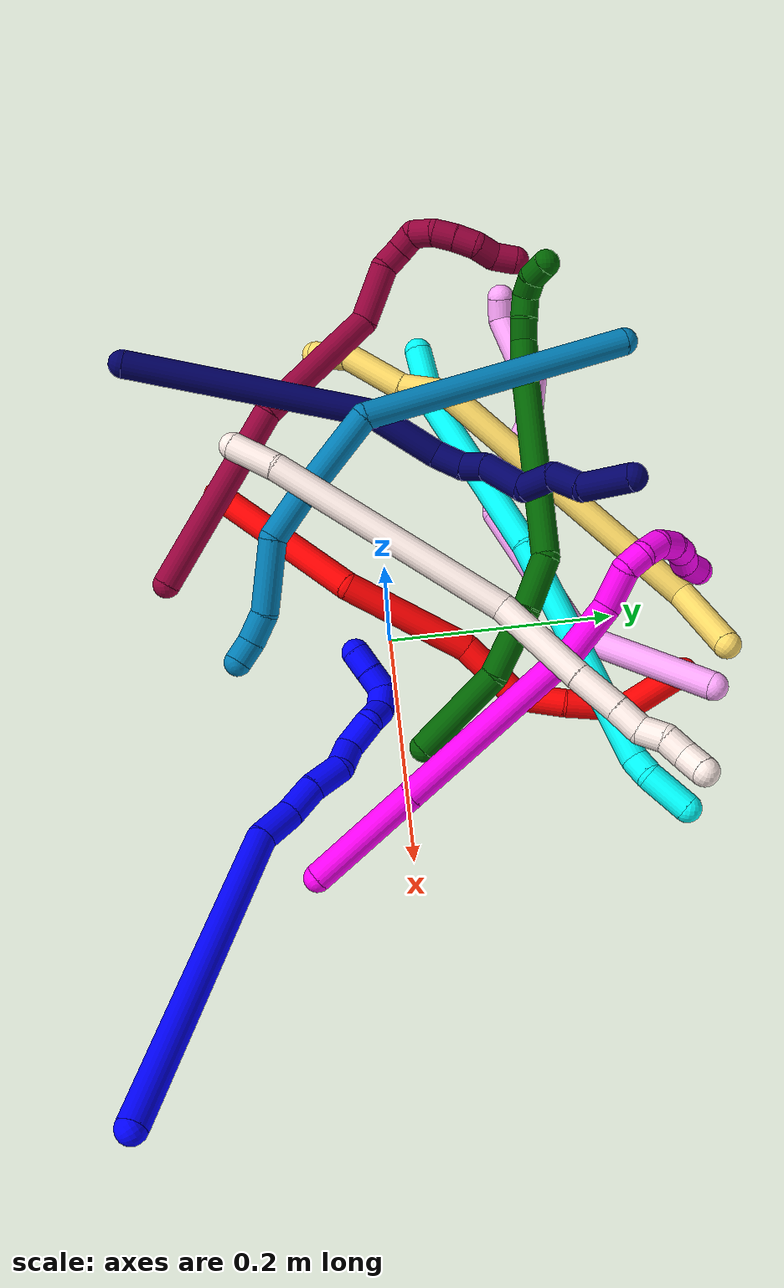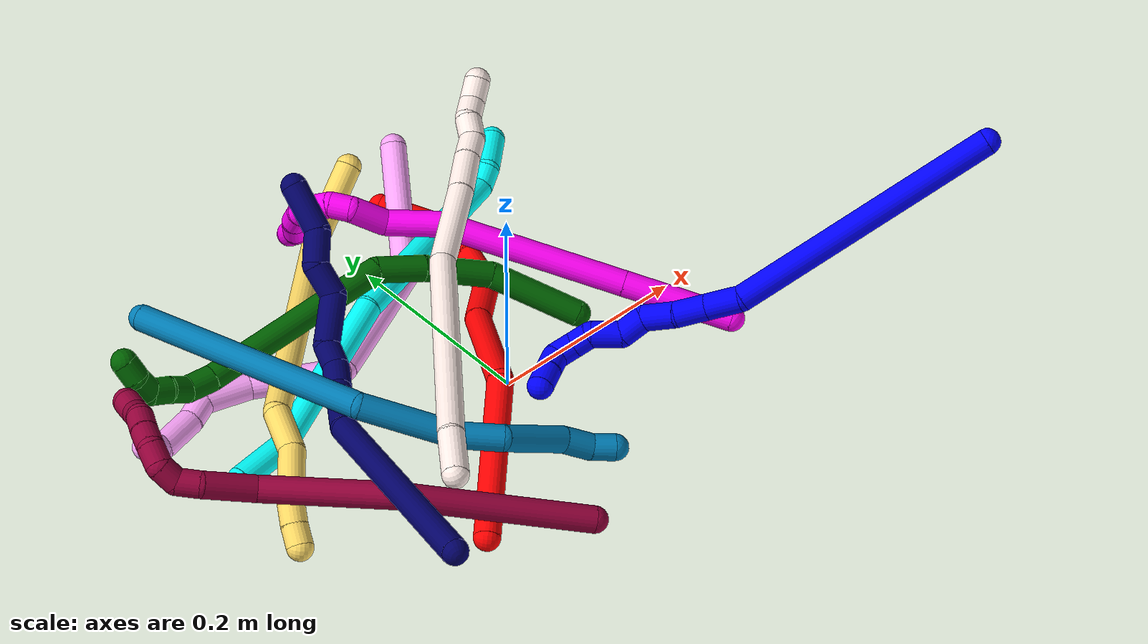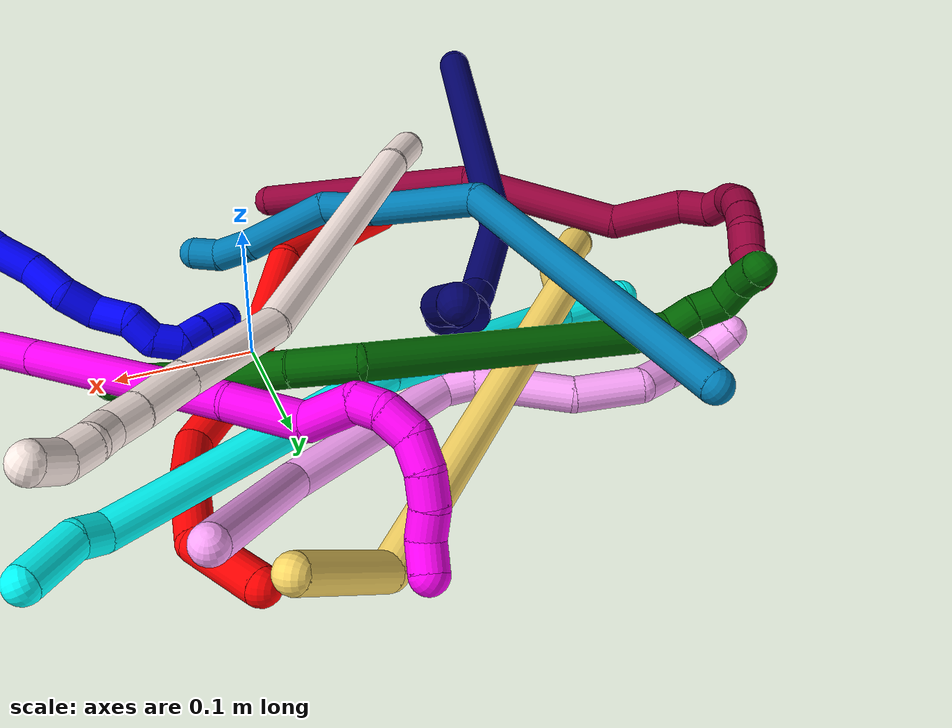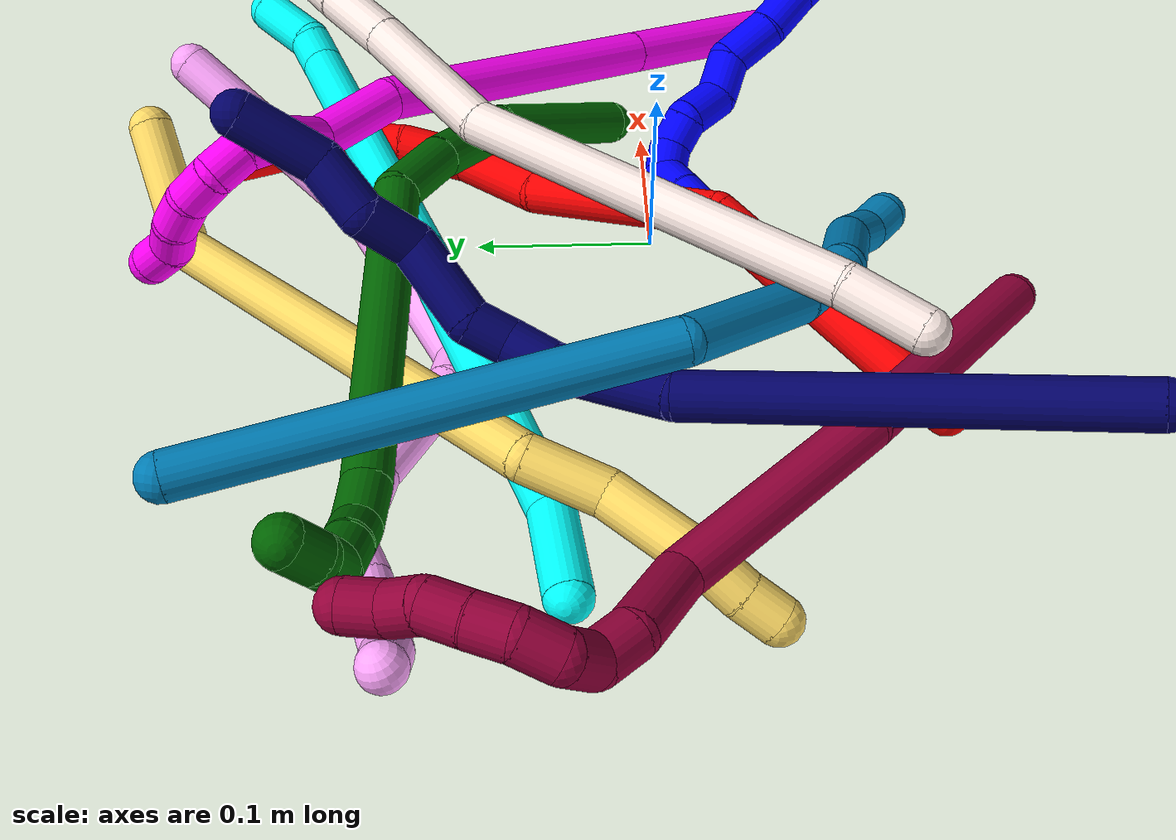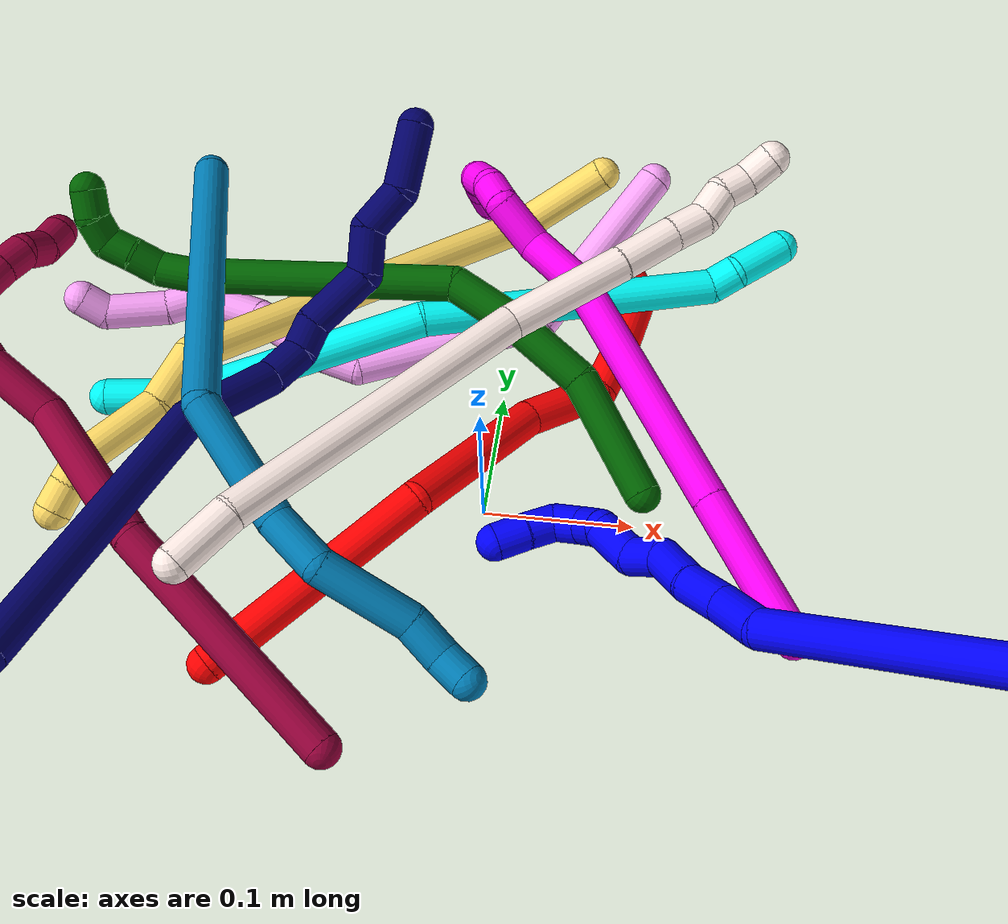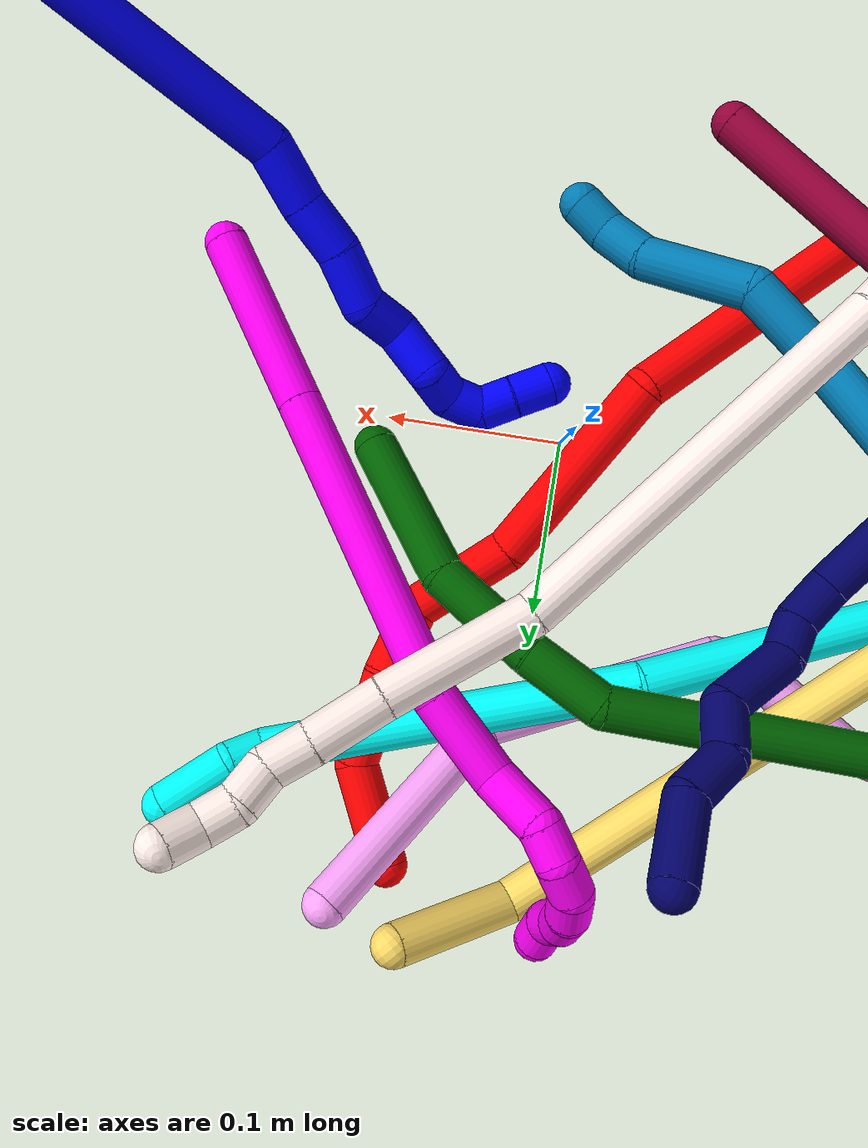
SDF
<sdf version="1.7">
 <world name="default">
  <plugin name="TubeGeneratorPlugin" filename="libtube_generator_plugin.so"/>
  <model name="photoneo_s_sensor">
   <static>1</static>
   <pose>0 0 2 1.57079 1.57079 3.14159</pose>
   <link name="link">
    <inertial><mass>0.1</mass></inertial>
    <sensor name="sensor" type="depth">
     <update_rate>30</update_rate>
     <camera>
      <horizontal_fov>1.22</horizontal_fov>
      <image><width>1920</width><height>1200</height><format>B8G8R8</format></image>
      <clip><near>0.1</near><far>4</far></clip>
      <depth_camera><output>points</output></depth_camera>
     </camera>
     <plugin name="camera_plugin" filename="libgazebo_ros_depth_camera.so">
      <baseline>0.2</baseline>
      <alwaysOn>1</alwaysOn>
      <updateRate>0.0</updateRate>
      <cameraName>camera_ir</cameraName>
      <imageTopicName>/camera/color/image_raw</imageTopicName>
      <cameraInfoTopicName>/camera/color/camera_info</cameraInfoTopicName>
      <depthImageTopicName>/camera/depth/image_raw</depthImageTopicName>
      <depthImageCameraInfoTopicName>/camera/depth/camera_info</depthImageCameraInfoTopicName>
      <pointCloudTopicName>/camera/depth/points</pointCloudTopicName>
      <frameName>fr_optical</frameName>
      <pointCloudCutoff>0.1</pointCloudCutoff>
      <pointCloudCutoffMax>2.0</pointCloudCutoffMax>
      <distortionK1>0</distortionK1>
      <distortionK2>0</distortionK2>
      <distortionK3>0</distortionK3>
      <distortionT1>0</distortionT1>
      <distortionT2>0</distortionT2>
      <CxPrime>0</CxPrime>
      <Cx>0</Cx>
      <Cy>0</Cy>
      <focalLength>0</focalLength>
      <hackBaseline>0</hackBaseline>
     </plugin>
    </sensor>
   </link>
  </model>
  <gravity>0 0 -9.8</gravity>
  <magnetic_field>6e-06 2.3e-05 -4.2e-05</magnetic_field>
  <atmosphere type="adiabatic"/>
  <physics name="default_physics" default="0" type="ode">
   <max_step_size>0.003</max_step_size>
   <real_time_factor>1</real_time_factor>
   <real_time_update_rate>1000</real_time_update_rate>
   <max_contacts>10000</max_contacts>
   <ode>
    <solver>
     <type>quick</type>
     <iters>100</iters>
     <sor>1.3</sor>
     <use_dynamic_moi_rescaling>0</use_dynamic_moi_rescaling>
    </solver>
    <constraints>
     <contact_max_correcting_vel>0</contact_max_correcting_vel>
     <contact_surface_layer>0.001</contact_surface_layer>
     <cfm>0</cfm>
     <erp>0.2</erp>
    </constraints>
   </ode>
  </physics>
  <scene><ambient>0.4 0.4 0.4 1</ambient><background>0.7 0.7 0.7 1</background><shadows>0</shadows></scene>
  <audio><device>default</device></audio>
  <spherical_coordinates>
   <surface_model>EARTH_WGS84</surface_model>
   <latitude_deg>0</latitude_deg>
   <longitude_deg>0</longitude_deg>
   <elevation>0</elevation>
   <heading_deg>0</heading_deg>
  </spherical_coordinates>
  <model name="bin">
   <static>1</static>
   <link name="bottom">
    <collision name="collision-bottom">
     <pose>0 0 -0.01 0 -0 0</pose>
     <geometry><box><size>0.8 0.6 0.02</size></box></geometry>
     <surface>
      <friction><ode><mu>100</mu><mu2>100</mu2></ode></friction>
      <contact><collide_bitmask>65535</collide_bitmask></contact>
     </surface>
    </collision>
   </link>
   <link name="west_wall">
    <collision name="collision-west_wall">
     <pose>-0.41 0 0.1 0 -0 0</pose>
     <geometry><box><size>0.02 0.6 0.2</size></box></geometry>
     <surface>
      <friction><ode><mu>100</mu><mu2>100</mu2></ode></friction>
      <contact><collide_bitmask>65535</collide_bitmask></contact>
     </surface>
    </collision>
   </link>
   <link name="east_wall">
    <collision name="collision-east_wall">
     <pose>0.41 0 0.1 0 -0 0</pose>
     <geometry><box><size>0.02 0.6 0.2</size></box></geometry>
     <surface>
      <friction><ode><mu>100</mu><mu2>100</mu2></ode></friction>
      <contact><collide_bitmask>65535</collide_bitmask></contact>
     </surface>
    </collision>
   </link>
   <link name="south_wall">
    <collision name="collision-south_wall">
     <pose>0 -0.31 0.1 0 -0 0</pose>
     <geometry><box><size>0.8 0.02 0.2</size></box></geometry>
     <surface>
      <friction><ode><mu>100</mu><mu2>100</mu2></ode></friction>
      <contact><collide_bitmask>65535</collide_bitmask></contact>
     </surface>
    </collision>
   </link>
   <link name="north_wall">
    <collision name="collision-north_wall">
     <pose>0 0.31 0.1 0 -0 0</pose>
     <geometry><box><size>0.8 0.02 0.2</size></box></geometry>
     <surface>
      <friction><ode><mu>100</mu><mu2>100</mu2></ode></friction>
      <contact><collide_bitmask>65535</collide_bitmask></contact>
     </surface>
    </collision>
   </link>
  </model>
  <model name="1">
   <static>0</static>
   <link name="1">
    <collision name="collision-cylinder-e_1_1_4">
     <pose>-0.076024 0.046349 -0.098505 -2.70181 -0.609606 1.9062</pose>
     <geometry><cylinder><radius>0.0125</radius><length>0.265564</length></cylinder></geometry>
     <surface>
      <friction><ode><mu>1.16</mu><mu2>1.16</mu2><slip1>0</slip1><slip2>0</slip2></ode></friction>
      <contact><ode><kp>1e+06</kp><kd>1</kd><max_vel>0</max_vel><min_depth>0.001</min_depth></ode></contact>
     </surface>
    </collision>
    <visual name="visual-cylinder-e_1_1_4">
     <pose>-0.076024 0.046349 -0.098505 -2.70181 -0.609606 1.9062</pose>
     <geometry><cylinder><radius>0.0125</radius><length>0.265564</length></cylinder></geometry>
     <material><ambient>0 0 1 1</ambient></material>
    </visual>
    <collision name="collision-cylinder-e_2_4_5">
     <pose>-0.158288 0.09359 -0.212978 -3.08571 -0.372092 2.84677</pose>
     <geometry><cylinder><radius>0.0125</radius><length>0.034335</length></cylinder></geometry>
     <surface>
      <friction><ode><mu>1.16</mu><mu2>1.16</mu2><slip1>0</slip1><slip2>0</slip2></ode></friction>
      <contact><ode><kp>1e+06</kp><kd>1</kd><max_vel>0</max_vel><min_depth>0.001</min_depth></ode></contact>
     </surface>
    </collision>
    <visual name="visual-cylinder-e_2_4_5">
     <pose>-0.158288 0.09359 -0.212978 -3.08571 -0.372092 2.84677</pose>
     <geometry><cylinder><radius>0.0125</radius><length>0.034335</length></cylinder></geometry>
     <material><ambient>0 0 1 1</ambient></material>
    </visual>
    <collision name="collision-cylinder-e_3_5_6">
     <pose>-0.169473 0.097666 -0.243044 -2.91956 -0.329509 1.96033</pose>
     <geometry><cylinder><radius>0.0125</radius><length>0.030552</length></cylinder></geometry>
     <surface>
      <friction><ode><mu>1.16</mu><mu2>1.16</mu2><slip1>0</slip1><slip2>0</slip2></ode></friction>
      <contact><ode><kp>1e+06</kp><kd>1</kd><max_vel>0</max_vel><min_depth>0.001</min_depth></ode></contact>
     </surface>
    </collision>
    <visual name="visual-cylinder-e_3_5_6">
     <pose>-0.169473 0.097666 -0.243044 -2.91956 -0.329509 1.96033</pose>
     <geometry><cylinder><radius>0.0125</radius><length>0.030552</length></cylinder></geometry>
     <material><ambient>0 0 1 1</ambient></material>
    </visual>
    <collision name="collision-cylinder-e_4_6_7">
     <pose>-0.178429 0.100951 -0.272412 -3.13491 -0.257003 3.08991</pose>
     <geometry><cylinder><radius>0.0125</radius><length>0.031575</length></cylinder></geometry>
     <surface>
      <friction><ode><mu>1.16</mu><mu2>1.16</mu2><slip1>0</slip1><slip2>0</slip2></ode></friction>
      <contact><ode><kp>1e+06</kp><kd>1</kd><max_vel>0</max_vel><min_depth>0.001</min_depth></ode></contact>
     </surface>
    </collision>
    <visual name="visual-cylinder-e_4_6_7">
     <pose>-0.178429 0.100951 -0.272412 -3.13491 -0.257003 3.08991</pose>
     <geometry><cylinder><radius>0.0125</radius><length>0.031575</length></cylinder></geometry>
     <material><ambient>0 0 1 1</ambient></material>
    </visual>
    <collision name="collision-cylinder-e_5_7_8">
     <pose>-0.190799 0.104793 -0.296889 -2.75581 -0.699199 2.15792</pose>
     <geometry><cylinder><radius>0.0125</radius><length>0.025971</length></cylinder></geometry>
     <surface>
      <friction><ode><mu>1.16</mu><mu2>1.16</mu2><slip1>0</slip1><slip2>0</slip2></ode></friction>
      <contact><ode><kp>1e+06</kp><kd>1</kd><max_vel>0</max_vel><min_depth>0.001</min_depth></ode></contact>
     </surface>
    </collision>
    <visual name="visual-cylinder-e_5_7_8">
     <pose>-0.190799 0.104793 -0.296889 -2.75581 -0.699199 2.15792</pose>
     <geometry><cylinder><radius>0.0125</radius><length>0.025971</length></cylinder></geometry>
     <material><ambient>0 0 1 1</ambient></material>
    </visual>
    <collision name="collision-cylinder-e_6_8_9">
     <pose>-0.199636 0.113355 -0.31966 -2.80002 -0.033324 0.192641</pose>
     <geometry><cylinder><radius>0.0125</radius><length>0.028805</length></cylinder></geometry>
     <surface>
      <friction><ode><mu>1.16</mu><mu2>1.16</mu2><slip1>0</slip1><slip2>0</slip2></ode></friction>
      <contact><ode><kp>1e+06</kp><kd>1</kd><max_vel>0</max_vel><min_depth>0.001</min_depth></ode></contact>
     </surface>
    </collision>
    <visual name="visual-cylinder-e_6_8_9">
     <pose>-0.199636 0.113355 -0.31966 -2.80002 -0.033324 0.192641</pose>
     <geometry><cylinder><radius>0.0125</radius><length>0.028805</length></cylinder></geometry>
     <material><ambient>0 0 1 1</ambient></material>
    </visual>
    <collision name="collision-cylinder-e_7_9_10">
     <pose>-0.206391 0.118673 -0.341214 -3.07951 -0.664738 2.96217</pose>
     <geometry><cylinder><radius>0.0125</radius><length>0.020345</length></cylinder></geometry>
     <surface>
      <friction><ode><mu>1.16</mu><mu2>1.16</mu2><slip1>0</slip1><slip2>0</slip2></ode></friction>
      <contact><ode><kp>1e+06</kp><kd>1</kd><max_vel>0</max_vel><min_depth>0.001</min_depth></ode></contact>
     </surface>
    </collision>
    <visual name="visual-cylinder-e_7_9_10">
     <pose>-0.206391 0.118673 -0.341214 -3.07951 -0.664738 2.96217</pose>
     <geometry><cylinder><radius>0.0125</radius><length>0.020345</length></cylinder></geometry>
     <material><ambient>0 0 1 1</ambient></material>
    </visual>
    <collision name="collision-cylinder-e_8_10_11">
     <pose>-0.217336 0.125432 -0.355887 -2.38857 -0.471632 1.09219</pose>
     <geometry><cylinder><radius>0.0125</radius><length>0.020558</length></cylinder></geometry>
     <surface>
      <friction><ode><mu>1.16</mu><mu2>1.16</mu2><slip1>0</slip1><slip2>0</slip2></ode></friction>
      <contact><ode><kp>1e+06</kp><kd>1</kd><max_vel>0</max_vel><min_depth>0.001</min_depth></ode></contact>
     </surface>
    </collision>
    <visual name="visual-cylinder-e_8_10_11">
     <pose>-0.217336 0.125432 -0.355887 -2.38857 -0.471632 1.09219</pose>
     <geometry><cylinder><radius>0.0125</radius><length>0.020558</length></cylinder></geometry>
     <material><ambient>0 0 1 1</ambient></material>
    </visual>
    <collision name="collision-cylinder-e_9_11_12">
     <pose>-0.225558 0.141169 -0.36231 -1.54361 -0.358451 0.349032</pose>
     <geometry><cylinder><radius>0.0125</radius><length>0.020244</length></cylinder></geometry>
     <surface>
      <friction><ode><mu>1.16</mu><mu2>1.16</mu2><slip1>0</slip1><slip2>0</slip2></ode></friction>
      <contact><ode><kp>1e+06</kp><kd>1</kd><max_vel>0</max_vel><min_depth>0.001</min_depth></ode></contact>
     </surface>
    </collision>
    <visual name="visual-cylinder-e_9_11_12">
     <pose>-0.225558 0.141169 -0.36231 -1.54361 -0.358451 0.349032</pose>
     <geometry><cylinder><radius>0.0125</radius><length>0.020244</length></cylinder></geometry>
     <material><ambient>0 0 1 1</ambient></material>
    </visual>
    <collision name="collision-cylinder-e_10_12_2">
     <pose>-0.233752 0.160643 -0.361938 -1.55937 -0.434708 0.429921</pose>
     <geometry><cylinder><radius>0.0125</radius><length>0.022052</length></cylinder></geometry>
     <surface>
      <friction><ode><mu>1.16</mu><mu2>1.16</mu2><slip1>0</slip1><slip2>0</slip2></ode></friction>
      <contact><ode><kp>1e+06</kp><kd>1</kd><max_vel>0</max_vel><min_depth>0.001</min_depth></ode></contact>
     </surface>
    </collision>
    <visual name="visual-cylinder-e_10_12_2">
     <pose>-0.233752 0.160643 -0.361938 -1.55937 -0.434708 0.429921</pose>
     <geometry><cylinder><radius>0.0125</radius><length>0.022052</length></cylinder></geometry>
     <material><ambient>0 0 1 1</ambient></material>
    </visual>
    <collision name="collision-sphere-2">
     <pose>-0.238396 0.170643 -0.361824 0 -0 0</pose>
     <geometry><sphere><radius>0.0125</radius></sphere></geometry>
     <surface>
      <friction><ode><mu>1.16</mu><mu2>1.16</mu2><slip1>0</slip1><slip2>0</slip2></ode></friction>
      <contact><ode><kp>1e+06</kp><kd>1</kd><max_vel>0</max_vel><min_depth>0.001</min_depth></ode></contact>
     </surface>
    </collision>
    <visual name="visual-sphere-2">
     <pose>-0.238396 0.170643 -0.361824 0 -0 0</pose>
     <geometry><sphere><radius>0.0125</radius></sphere></geometry>
     <material><ambient>0 0 1 1</ambient></material>
    </visual>
    <collision name="collision-sphere-12">
     <pose>-0.229109 0.150644 -0.362052 0 -0 0</pose>
     <geometry><sphere><radius>0.0125</radius></sphere></geometry>
     <surface>
      <friction><ode><mu>1.16</mu><mu2>1.16</mu2><slip1>0</slip1><slip2>0</slip2></ode></friction>
      <contact><ode><kp>1e+06</kp><kd>1</kd><max_vel>0</max_vel><min_depth>0.001</min_depth></ode></contact>
     </surface>
    </collision>
    <visual name="visual-sphere-12">
     <pose>-0.229109 0.150644 -0.362052 0 -0 0</pose>
     <geometry><sphere><radius>0.0125</radius></sphere></geometry>
     <material><ambient>0 0 1 1</ambient></material>
    </visual>
    <collision name="collision-sphere-11">
     <pose>-0.222007 0.131694 -0.362568 0 -0 0</pose>
     <geometry><sphere><radius>0.0125</radius></sphere></geometry>
     <surface>
      <friction><ode><mu>1.16</mu><mu2>1.16</mu2><slip1>0</slip1><slip2>0</slip2></ode></friction>
      <contact><ode><kp>1e+06</kp><kd>1</kd><max_vel>0</max_vel><min_depth>0.001</min_depth></ode></contact>
     </surface>
    </collision>
    <visual name="visual-sphere-11">
     <pose>-0.222007 0.131694 -0.362568 0 -0 0</pose>
     <geometry><sphere><radius>0.0125</radius></sphere></geometry>
     <material><ambient>0 0 1 1</ambient></material>
    </visual>
    <collision name="collision-sphere-10">
     <pose>-0.212666 0.11917 -0.349206 0 -0 0</pose>
     <geometry><sphere><radius>0.0125</radius></sphere></geometry>
     <surface>
      <friction><ode><mu>1.16</mu><mu2>1.16</mu2><slip1>0</slip1><slip2>0</slip2></ode></friction>
      <contact><ode><kp>1e+06</kp><kd>1</kd><max_vel>0</max_vel><min_depth>0.001</min_depth></ode></contact>
     </surface>
    </collision>
    <visual name="visual-sphere-10">
     <pose>-0.212666 0.11917 -0.349206 0 -0 0</pose>
     <geometry><sphere><radius>0.0125</radius></sphere></geometry>
     <material><ambient>0 0 1 1</ambient></material>
    </visual>
    <collision name="collision-sphere-9">
     <pose>-0.200116 0.118176 -0.333223 0 -0 0</pose>
     <geometry><sphere><radius>0.0125</radius></sphere></geometry>
     <surface>
      <friction><ode><mu>1.16</mu><mu2>1.16</mu2><slip1>0</slip1><slip2>0</slip2></ode></friction>
      <contact><ode><kp>1e+06</kp><kd>1</kd><max_vel>0</max_vel><min_depth>0.001</min_depth></ode></contact>
     </surface>
    </collision>
    <visual name="visual-sphere-9">
     <pose>-0.200116 0.118176 -0.333223 0 -0 0</pose>
     <geometry><sphere><radius>0.0125</radius></sphere></geometry>
     <material><ambient>0 0 1 1</ambient></material>
    </visual>
    <collision name="collision-sphere-4">
     <pose>-0.152047 0.092697 -0.19701 0 -0 0</pose>
     <geometry><sphere><radius>0.0125</radius></sphere></geometry>
     <surface>
      <friction><ode><mu>1.16</mu><mu2>1.16</mu2><slip1>0</slip1><slip2>0</slip2></ode></friction>
      <contact><ode><kp>1e+06</kp><kd>1</kd><max_vel>0</max_vel><min_depth>0.001</min_depth></ode></contact>
     </surface>
    </collision>
    <visual name="visual-sphere-4">
     <pose>-0.152047 0.092697 -0.19701 0 -0 0</pose>
     <geometry><sphere><radius>0.0125</radius></sphere></geometry>
     <material><ambient>0 0 1 1</ambient></material>
    </visual>
    <collision name="collision-sphere-1">
     <geometry><sphere><radius>0.0125</radius></sphere></geometry>
     <surface>
      <friction><ode><mu>1.16</mu><mu2>1.16</mu2><slip1>0</slip1><slip2>0</slip2></ode></friction>
      <contact><ode><kp>1e+06</kp><kd>1</kd><max_vel>0</max_vel><min_depth>0.001</min_depth></ode></contact>
     </surface>
    </collision>
    <visual name="visual-sphere-1">
     <geometry><sphere><radius>0.0125</radius></sphere></geometry>
     <material><ambient>0 0 1 1</ambient></material>
    </visual>
    <collision name="collision-sphere-8">
     <pose>-0.199156 0.108533 -0.306097 0 -0 0</pose>
     <geometry><sphere><radius>0.0125</radius></sphere></geometry>
     <surface>
      <friction><ode><mu>1.16</mu><mu2>1.16</mu2><slip1>0</slip1><slip2>0</slip2></ode></friction>
      <contact><ode><kp>1e+06</kp><kd>1</kd><max_vel>0</max_vel><min_depth>0.001</min_depth></ode></contact>
     </surface>
    </collision>
    <visual name="visual-sphere-8">
     <pose>-0.199156 0.108533 -0.306097 0 -0 0</pose>
     <geometry><sphere><radius>0.0125</radius></sphere></geometry>
     <material><ambient>0 0 1 1</ambient></material>
    </visual>
    <collision name="collision-sphere-5">
     <pose>-0.16453 0.094484 -0.228945 0 -0 0</pose>
     <geometry><sphere><radius>0.0125</radius></sphere></geometry>
     <surface>
      <friction><ode><mu>1.16</mu><mu2>1.16</mu2><slip1>0</slip1><slip2>0</slip2></ode></friction>
      <contact><ode><kp>1e+06</kp><kd>1</kd><max_vel>0</max_vel><min_depth>0.001</min_depth></ode></contact>
     </surface>
    </collision>
    <visual name="visual-sphere-5">
     <pose>-0.16453 0.094484 -0.228945 0 -0 0</pose>
     <geometry><sphere><radius>0.0125</radius></sphere></geometry>
     <material><ambient>0 0 1 1</ambient></material>
    </visual>
    <collision name="collision-sphere-6">
     <pose>-0.174416 0.100849 -0.257144 0 -0 0</pose>
     <geometry><sphere><radius>0.0125</radius></sphere></geometry>
     <surface>
      <friction><ode><mu>1.16</mu><mu2>1.16</mu2><slip1>0</slip1><slip2>0</slip2></ode></friction>
      <contact><ode><kp>1e+06</kp><kd>1</kd><max_vel>0</max_vel><min_depth>0.001</min_depth></ode></contact>
     </surface>
    </collision>
    <visual name="visual-sphere-6">
     <pose>-0.174416 0.100849 -0.257144 0 -0 0</pose>
     <geometry><sphere><radius>0.0125</radius></sphere></geometry>
     <material><ambient>0 0 1 1</ambient></material>
    </visual>
    <collision name="collision-sphere-7">
     <pose>-0.182442 0.101053 -0.287681 0 -0 0</pose>
     <geometry><sphere><radius>0.0125</radius></sphere></geometry>
     <surface>
      <friction><ode><mu>1.16</mu><mu2>1.16</mu2><slip1>0</slip1><slip2>0</slip2></ode></friction>
      <contact><ode><kp>1e+06</kp><kd>1</kd><max_vel>0</max_vel><min_depth>0.001</min_depth></ode></contact>
     </surface>
    </collision>
    <visual name="visual-sphere-7">
     <pose>-0.182442 0.101053 -0.287681 0 -0 0</pose>
     <geometry><sphere><radius>0.0125</radius></sphere></geometry>
     <material><ambient>0 0 1 1</ambient></material>
    </visual>
    <inertial>
     <pose>-0.131058 0.078147 -0.191983 0 -0 0</pose>
     <mass>0.5</mass>
     <inertia>
      <ixx>0.000778</ixx>
      <ixy>0</ixy>
      <ixz>0</ixz>
      <iyy>0.002079</iyy>
      <iyz>0</iyz>
      <izz>0.000325</izz>
     </inertia>
    </inertial>
   </link>
   <pose>0.391552 -0.217238 0.2078 1.27475 -1.15847 0.757304</pose>
  </model>
  <model name="2">
   <static>0</static>
   <link name="2">
    <collision name="collision-cylinder-e_1_1_4">
     <pose>0.044298 0.06902 0.000218 -1.56764 0.570599 -0.568895</pose>
     <geometry><cylinder><radius>0.0125</radius><length>0.164027</length></cylinder></geometry>
     <surface>
      <friction><ode><mu>1.16</mu><mu2>1.16</mu2><slip1>0</slip1><slip2>0</slip2></ode></friction>
      <contact><ode><kp>1e+06</kp><kd>1</kd><max_vel>0</max_vel><min_depth>0.001</min_depth></ode></contact>
     </surface>
    </collision>
    <visual name="visual-cylinder-e_1_1_4">
     <pose>0.044298 0.06902 0.000218 -1.56764 0.570599 -0.568895</pose>
     <geometry><cylinder><radius>0.0125</radius><length>0.164027</length></cylinder></geometry>
     <material><ambient>1 0 0 1</ambient></material>
    </visual>
    <collision name="collision-cylinder-e_2_4_5">
     <pose>0.090915 0.195568 0.011913 -1.37387 0.039492 -0.032392</pose>
     <geometry><cylinder><radius>0.0125</radius><length>0.117413</length></cylinder></geometry>
     <surface>
      <friction><ode><mu>1.16</mu><mu2>1.16</mu2><slip1>0</slip1><slip2>0</slip2></ode></friction>
      <contact><ode><kp>1e+06</kp><kd>1</kd><max_vel>0</max_vel><min_depth>0.001</min_depth></ode></contact>
     </surface>
    </collision>
    <visual name="visual-cylinder-e_2_4_5">
     <pose>0.090915 0.195568 0.011913 -1.37387 0.039492 -0.032392</pose>
     <geometry><cylinder><radius>0.0125</radius><length>0.117413</length></cylinder></geometry>
     <material><ambient>1 0 0 1</ambient></material>
    </visual>
    <collision name="collision-cylinder-e_3_5_6">
     <pose>0.097254 0.283815 0.020418 -1.66725 0.129566 -0.142664</pose>
     <geometry><cylinder><radius>0.0125</radius><length>0.062249</length></cylinder></geometry>
     <surface>
      <friction><ode><mu>1.16</mu><mu2>1.16</mu2><slip1>0</slip1><slip2>0</slip2></ode></friction>
      <contact><ode><kp>1e+06</kp><kd>1</kd><max_vel>0</max_vel><min_depth>0.001</min_depth></ode></contact>
     </surface>
    </collision>
    <visual name="visual-cylinder-e_3_5_6">
     <pose>0.097254 0.283815 0.020418 -1.66725 0.129566 -0.142664</pose>
     <geometry><cylinder><radius>0.0125</radius><length>0.062249</length></cylinder></geometry>
     <material><ambient>1 0 0 1</ambient></material>
    </visual>
    <collision name="collision-cylinder-e_4_6_7">
     <pose>0.108003 0.331761 0.027427 -1.04564 0.325873 -0.188921</pose>
     <geometry><cylinder><radius>0.0125</radius><length>0.042029</length></cylinder></geometry>
     <surface>
      <friction><ode><mu>1.16</mu><mu2>1.16</mu2><slip1>0</slip1><slip2>0</slip2></ode></friction>
      <contact><ode><kp>1e+06</kp><kd>1</kd><max_vel>0</max_vel><min_depth>0.001</min_depth></ode></contact>
     </surface>
    </collision>
    <visual name="visual-cylinder-e_4_6_7">
     <pose>0.108003 0.331761 0.027427 -1.04564 0.325873 -0.188921</pose>
     <geometry><cylinder><radius>0.0125</radius><length>0.042029</length></cylinder></geometry>
     <material><ambient>1 0 0 1</ambient></material>
    </visual>
    <collision name="collision-cylinder-e_5_7_8">
     <pose>0.117907 0.37122 0.052562 -0.972538 0.117545 -0.062186</pose>
     <geometry><cylinder><radius>0.0125</radius><length>0.054186</length></cylinder></geometry>
     <surface>
      <friction><ode><mu>1.16</mu><mu2>1.16</mu2><slip1>0</slip1><slip2>0</slip2></ode></friction>
      <contact><ode><kp>1e+06</kp><kd>1</kd><max_vel>0</max_vel><min_depth>0.001</min_depth></ode></contact>
     </surface>
    </collision>
    <visual name="visual-cylinder-e_5_7_8">
     <pose>0.117907 0.37122 0.052562 -0.972538 0.117545 -0.062186</pose>
     <geometry><cylinder><radius>0.0125</radius><length>0.054186</length></cylinder></geometry>
     <material><ambient>1 0 0 1</ambient></material>
    </visual>
    <collision name="collision-cylinder-e_6_8_2">
     <pose>0.123291 0.403712 0.095871 -0.349423 0.073478 -0.012975</pose>
     <geometry><cylinder><radius>0.0125</radius><length>0.060096</length></cylinder></geometry>
     <surface>
      <friction><ode><mu>1.16</mu><mu2>1.16</mu2><slip1>0</slip1><slip2>0</slip2></ode></friction>
      <contact><ode><kp>1e+06</kp><kd>1</kd><max_vel>0</max_vel><min_depth>0.001</min_depth></ode></contact>
     </surface>
    </collision>
    <visual name="visual-cylinder-e_6_8_2">
     <pose>0.123291 0.403712 0.095871 -0.349423 0.073478 -0.012975</pose>
     <geometry><cylinder><radius>0.0125</radius><length>0.060096</length></cylinder></geometry>
     <material><ambient>1 0 0 1</ambient></material>
    </visual>
    <collision name="collision-sphere-2">
     <pose>0.125497 0.413971 0.124027 0 -0 0</pose>
     <geometry><sphere><radius>0.0125</radius></sphere></geometry>
     <surface>
      <friction><ode><mu>1.16</mu><mu2>1.16</mu2><slip1>0</slip1><slip2>0</slip2></ode></friction>
      <contact><ode><kp>1e+06</kp><kd>1</kd><max_vel>0</max_vel><min_depth>0.001</min_depth></ode></contact>
     </surface>
    </collision>
    <visual name="visual-sphere-2">
     <pose>0.125497 0.413971 0.124027 0 -0 0</pose>
     <geometry><sphere><radius>0.0125</radius></sphere></geometry>
     <material><ambient>1 0 0 1</ambient></material>
    </visual>
    <collision name="collision-sphere-4">
     <pose>0.088597 0.138041 0.000436 0 -0 0</pose>
     <geometry><sphere><radius>0.0125</radius></sphere></geometry>
     <surface>
      <friction><ode><mu>1.16</mu><mu2>1.16</mu2><slip1>0</slip1><slip2>0</slip2></ode></friction>
      <contact><ode><kp>1e+06</kp><kd>1</kd><max_vel>0</max_vel><min_depth>0.001</min_depth></ode></contact>
     </surface>
    </collision>
    <visual name="visual-sphere-4">
     <pose>0.088597 0.138041 0.000436 0 -0 0</pose>
     <geometry><sphere><radius>0.0125</radius></sphere></geometry>
     <material><ambient>1 0 0 1</ambient></material>
    </visual>
    <collision name="collision-sphere-1">
     <geometry><sphere><radius>0.0125</radius></sphere></geometry>
     <surface>
      <friction><ode><mu>1.16</mu><mu2>1.16</mu2><slip1>0</slip1><slip2>0</slip2></ode></friction>
      <contact><ode><kp>1e+06</kp><kd>1</kd><max_vel>0</max_vel><min_depth>0.001</min_depth></ode></contact>
     </surface>
    </collision>
    <visual name="visual-sphere-1">
     <geometry><sphere><radius>0.0125</radius></sphere></geometry>
     <material><ambient>1 0 0 1</ambient></material>
    </visual>
    <collision name="collision-sphere-8">
     <pose>0.121085 0.393453 0.067715 0 -0 0</pose>
     <geometry><sphere><radius>0.0125</radius></sphere></geometry>
     <surface>
      <friction><ode><mu>1.16</mu><mu2>1.16</mu2><slip1>0</slip1><slip2>0</slip2></ode></friction>
      <contact><ode><kp>1e+06</kp><kd>1</kd><max_vel>0</max_vel><min_depth>0.001</min_depth></ode></contact>
     </surface>
    </collision>
    <visual name="visual-sphere-8">
     <pose>0.121085 0.393453 0.067715 0 -0 0</pose>
     <geometry><sphere><radius>0.0125</radius></sphere></geometry>
     <material><ambient>1 0 0 1</ambient></material>
    </visual>
    <collision name="collision-sphere-5">
     <pose>0.093232 0.253095 0.02339 0 -0 0</pose>
     <geometry><sphere><radius>0.0125</radius></sphere></geometry>
     <surface>
      <friction><ode><mu>1.16</mu><mu2>1.16</mu2><slip1>0</slip1><slip2>0</slip2></ode></friction>
      <contact><ode><kp>1e+06</kp><kd>1</kd><max_vel>0</max_vel><min_depth>0.001</min_depth></ode></contact>
     </surface>
    </collision>
    <visual name="visual-sphere-5">
     <pose>0.093232 0.253095 0.02339 0 -0 0</pose>
     <geometry><sphere><radius>0.0125</radius></sphere></geometry>
     <material><ambient>1 0 0 1</ambient></material>
    </visual>
    <collision name="collision-sphere-6">
     <pose>0.101275 0.314535 0.017446 0 -0 0</pose>
     <geometry><sphere><radius>0.0125</radius></sphere></geometry>
     <surface>
      <friction><ode><mu>1.16</mu><mu2>1.16</mu2><slip1>0</slip1><slip2>0</slip2></ode></friction>
      <contact><ode><kp>1e+06</kp><kd>1</kd><max_vel>0</max_vel><min_depth>0.001</min_depth></ode></contact>
     </surface>
    </collision>
    <visual name="visual-sphere-6">
     <pose>0.101275 0.314535 0.017446 0 -0 0</pose>
     <geometry><sphere><radius>0.0125</radius></sphere></geometry>
     <material><ambient>1 0 0 1</ambient></material>
    </visual>
    <collision name="collision-sphere-7">
     <pose>0.11473 0.348987 0.037408 0 -0 0</pose>
     <geometry><sphere><radius>0.0125</radius></sphere></geometry>
     <surface>
      <friction><ode><mu>1.16</mu><mu2>1.16</mu2><slip1>0</slip1><slip2>0</slip2></ode></friction>
      <contact><ode><kp>1e+06</kp><kd>1</kd><max_vel>0</max_vel><min_depth>0.001</min_depth></ode></contact>
     </surface>
    </collision>
    <visual name="visual-sphere-7">
     <pose>0.11473 0.348987 0.037408 0 -0 0</pose>
     <geometry><sphere><radius>0.0125</radius></sphere></geometry>
     <material><ambient>1 0 0 1</ambient></material>
    </visual>
    <inertial>
     <pose>0.084664 0.220541 0.024936 0 -0 0</pose>
     <mass>0.5</mass>
     <inertia><ixx>0.000299</ixx><ixy>0</ixy><ixz>0</ixz><iyy>2e-05</iyy><iyz>0</iyz><izz>-0.000706</izz></inertia>
    </inertial>
   </link>
   <pose>-0.151588 -0.14231 0.011497 -1.2081 -1.23252 0.452327</pose>
  </model>
  <model name="3">
   <static>0</static>
   <link name="3">
    <collision name="collision-cylinder-e_1_1_4">
     <pose>0.011632 0.007755 0.022831 -0.327449 0.449477 -0.075495</pose>
     <geometry><cylinder><radius>0.0125</radius><length>0.053542</length></cylinder></geometry>
     <surface>
      <friction><ode><mu>1.16</mu><mu2>1.16</mu2><slip1>0</slip1><slip2>0</slip2></ode></friction>
      <contact><ode><kp>1e+06</kp><kd>1</kd><max_vel>0</max_vel><min_depth>0.001</min_depth></ode></contact>
     </surface>
    </collision>
    <visual name="visual-cylinder-e_1_1_4">
     <pose>0.011632 0.007755 0.022831 -0.327449 0.449477 -0.075495</pose>
     <geometry><cylinder><radius>0.0125</radius><length>0.053542</length></cylinder></geometry>
     <material><ambient>0.003922 1 0.996078 1</ambient></material>
    </visual>
    <collision name="collision-cylinder-e_2_4_5">
     <pose>0.081481 0.044923 0.102981 -0.474108 0.734822 -0.185442</pose>
     <geometry><cylinder><radius>0.0125</radius><length>0.173663</length></cylinder></geometry>
     <surface>
      <friction><ode><mu>1.16</mu><mu2>1.16</mu2><slip1>0</slip1><slip2>0</slip2></ode></friction>
      <contact><ode><kp>1e+06</kp><kd>1</kd><max_vel>0</max_vel><min_depth>0.001</min_depth></ode></contact>
     </surface>
    </collision>
    <visual name="visual-cylinder-e_2_4_5">
     <pose>0.081481 0.044923 0.102981 -0.474108 0.734822 -0.185442</pose>
     <geometry><cylinder><radius>0.0125</radius><length>0.173663</length></cylinder></geometry>
     <material><ambient>0.003922 1 0.996078 1</ambient></material>
    </visual>
    <collision name="collision-cylinder-e_3_5_6">
     <pose>0.202326 0.090208 0.243627 -0.18822 0.635986 -0.062119</pose>
     <geometry><cylinder><radius>0.0125</radius><length>0.210882</length></cylinder></geometry>
     <surface>
      <friction><ode><mu>1.16</mu><mu2>1.16</mu2><slip1>0</slip1><slip2>0</slip2></ode></friction>
      <contact><ode><kp>1e+06</kp><kd>1</kd><max_vel>0</max_vel><min_depth>0.001</min_depth></ode></contact>
     </surface>
    </collision>
    <visual name="visual-cylinder-e_3_5_6">
     <pose>0.202326 0.090208 0.243627 -0.18822 0.635986 -0.062119</pose>
     <geometry><cylinder><radius>0.0125</radius><length>0.210882</length></cylinder></geometry>
     <material><ambient>0.003922 1 0.996078 1</ambient></material>
    </visual>
    <collision name="collision-cylinder-e_4_6_7">
     <pose>0.272541 0.110933 0.331905 -0.775597 0.830396 -0.356321</pose>
     <geometry><cylinder><radius>0.0125</radius><length>0.020552</length></cylinder></geometry>
     <surface>
      <friction><ode><mu>1.16</mu><mu2>1.16</mu2><slip1>0</slip1><slip2>0</slip2></ode></friction>
      <contact><ode><kp>1e+06</kp><kd>1</kd><max_vel>0</max_vel><min_depth>0.001</min_depth></ode></contact>
     </surface>
    </collision>
    <visual name="visual-cylinder-e_4_6_7">
     <pose>0.272541 0.110933 0.331905 -0.775597 0.830396 -0.356321</pose>
     <geometry><cylinder><radius>0.0125</radius><length>0.020552</length></cylinder></geometry>
     <material><ambient>0.003922 1 0.996078 1</ambient></material>
    </visual>
    <collision name="collision-cylinder-e_5_7_2">
     <pose>0.297929 0.117617 0.347217 -0.174827 1.03691 -0.099913</pose>
     <geometry><cylinder><radius>0.0125</radius><length>0.04136</length></cylinder></geometry>
     <surface>
      <friction><ode><mu>1.16</mu><mu2>1.16</mu2><slip1>0</slip1><slip2>0</slip2></ode></friction>
      <contact><ode><kp>1e+06</kp><kd>1</kd><max_vel>0</max_vel><min_depth>0.001</min_depth></ode></contact>
     </surface>
    </collision>
    <visual name="visual-cylinder-e_5_7_2">
     <pose>0.297929 0.117617 0.347217 -0.174827 1.03691 -0.099913</pose>
     <geometry><cylinder><radius>0.0125</radius><length>0.04136</length></cylinder></geometry>
     <material><ambient>0.003922 1 0.996078 1</ambient></material>
    </visual>
    <collision name="collision-sphere-2">
     <pose>0.315731 0.119447 0.357581 0 -0 0</pose>
     <geometry><sphere><radius>0.0125</radius></sphere></geometry>
     <surface>
      <friction><ode><mu>1.16</mu><mu2>1.16</mu2><slip1>0</slip1><slip2>0</slip2></ode></friction>
      <contact><ode><kp>1e+06</kp><kd>1</kd><max_vel>0</max_vel><min_depth>0.001</min_depth></ode></contact>
     </surface>
    </collision>
    <visual name="visual-sphere-2">
     <pose>0.315731 0.119447 0.357581 0 -0 0</pose>
     <geometry><sphere><radius>0.0125</radius></sphere></geometry>
     <material><ambient>0.003922 1 0.996078 1</ambient></material>
    </visual>
    <collision name="collision-sphere-7">
     <pose>0.280127 0.115786 0.336854 0 -0 0</pose>
     <geometry><sphere><radius>0.0125</radius></sphere></geometry>
     <surface>
      <friction><ode><mu>1.16</mu><mu2>1.16</mu2><slip1>0</slip1><slip2>0</slip2></ode></friction>
      <contact><ode><kp>1e+06</kp><kd>1</kd><max_vel>0</max_vel><min_depth>0.001</min_depth></ode></contact>
     </surface>
    </collision>
    <visual name="visual-sphere-7">
     <pose>0.280127 0.115786 0.336854 0 -0 0</pose>
     <geometry><sphere><radius>0.0125</radius></sphere></geometry>
     <material><ambient>0.003922 1 0.996078 1</ambient></material>
    </visual>
    <collision name="collision-sphere-6">
     <pose>0.264955 0.106079 0.326955 0 -0 0</pose>
     <geometry><sphere><radius>0.0125</radius></sphere></geometry>
     <surface>
      <friction><ode><mu>1.16</mu><mu2>1.16</mu2><slip1>0</slip1><slip2>0</slip2></ode></friction>
      <contact><ode><kp>1e+06</kp><kd>1</kd><max_vel>0</max_vel><min_depth>0.001</min_depth></ode></contact>
     </surface>
    </collision>
    <visual name="visual-sphere-6">
     <pose>0.264955 0.106079 0.326955 0 -0 0</pose>
     <geometry><sphere><radius>0.0125</radius></sphere></geometry>
     <material><ambient>0.003922 1 0.996078 1</ambient></material>
    </visual>
    <collision name="collision-sphere-5">
     <pose>0.139697 0.074336 0.160299 0 -0 0</pose>
     <geometry><sphere><radius>0.0125</radius></sphere></geometry>
     <surface>
      <friction><ode><mu>1.16</mu><mu2>1.16</mu2><slip1>0</slip1><slip2>0</slip2></ode></friction>
      <contact><ode><kp>1e+06</kp><kd>1</kd><max_vel>0</max_vel><min_depth>0.001</min_depth></ode></contact>
     </surface>
    </collision>
    <visual name="visual-sphere-5">
     <pose>0.139697 0.074336 0.160299 0 -0 0</pose>
     <geometry><sphere><radius>0.0125</radius></sphere></geometry>
     <material><ambient>0.003922 1 0.996078 1</ambient></material>
    </visual>
    <collision name="collision-sphere-1">
     <geometry><sphere><radius>0.0125</radius></sphere></geometry>
     <surface>
      <friction><ode><mu>1.16</mu><mu2>1.16</mu2><slip1>0</slip1><slip2>0</slip2></ode></friction>
      <contact><ode><kp>1e+06</kp><kd>1</kd><max_vel>0</max_vel><min_depth>0.001</min_depth></ode></contact>
     </surface>
    </collision>
    <visual name="visual-sphere-1">
     <geometry><sphere><radius>0.0125</radius></sphere></geometry>
     <material><ambient>0.003922 1 0.996078 1</ambient></material>
    </visual>
    <collision name="collision-sphere-4">
     <pose>0.023264 0.01551 0.045662 0 -0 0</pose>
     <geometry><sphere><radius>0.0125</radius></sphere></geometry>
     <surface>
      <friction><ode><mu>1.16</mu><mu2>1.16</mu2><slip1>0</slip1><slip2>0</slip2></ode></friction>
      <contact><ode><kp>1e+06</kp><kd>1</kd><max_vel>0</max_vel><min_depth>0.001</min_depth></ode></contact>
     </surface>
    </collision>
    <visual name="visual-sphere-4">
     <pose>0.023264 0.01551 0.045662 0 -0 0</pose>
     <geometry><sphere><radius>0.0125</radius></sphere></geometry>
     <material><ambient>0.003922 1 0.996078 1</ambient></material>
    </visual>
    <inertial>
     <pose>0.150727 0.068769 0.183331 0 -0 0</pose>
     <mass>0.5</mass>
     <inertia>
      <ixx>0.000898</ixx>
      <ixy>0</ixy>
      <ixz>0</ixz>
      <iyy>0.001123</iyy>
      <iyz>0</iyz>
      <izz>-0.001027</izz>
     </inertia>
    </inertial>
   </link>
   <pose>-0.271402 0.055576 0.018076 1.98915 -0.192715 1.23916</pose>
  </model>
  <model name="4">
   <static>0</static>
   <link name="4">
    <collision name="collision-cylinder-e_1_1_4">
     <pose>-0.034712 -0.035735 -0.045852 2.47956 -0.538292 -1.35271</pose>
     <geometry><cylinder><radius>0.0125</radius><length>0.135415</length></cylinder></geometry>
     <surface>
      <friction><ode><mu>1.16</mu><mu2>1.16</mu2><slip1>0</slip1><slip2>0</slip2></ode></friction>
      <contact><ode><kp>1e+06</kp><kd>1</kd><max_vel>0</max_vel><min_depth>0.001</min_depth></ode></contact>
     </surface>
    </collision>
    <visual name="visual-cylinder-e_1_1_4">
     <pose>-0.034712 -0.035735 -0.045852 2.47956 -0.538292 -1.35271</pose>
     <geometry><cylinder><radius>0.0125</radius><length>0.135415</length></cylinder></geometry>
     <material><ambient>1 0.65098 0.996078 1</ambient></material>
    </visual>
    <collision name="collision-cylinder-e_2_4_5">
     <pose>-0.132348 -0.092812 -0.107909 2.22025 -1.16821 -1.85363</pose>
     <geometry><cylinder><radius>0.0125</radius><length>0.136787</length></cylinder></geometry>
     <surface>
      <friction><ode><mu>1.16</mu><mu2>1.16</mu2><slip1>0</slip1><slip2>0</slip2></ode></friction>
      <contact><ode><kp>1e+06</kp><kd>1</kd><max_vel>0</max_vel><min_depth>0.001</min_depth></ode></contact>
     </surface>
    </collision>
    <visual name="visual-cylinder-e_2_4_5">
     <pose>-0.132348 -0.092812 -0.107909 2.22025 -1.16821 -1.85363</pose>
     <geometry><cylinder><radius>0.0125</radius><length>0.136787</length></cylinder></geometry>
     <material><ambient>1 0.65098 0.996078 1</ambient></material>
    </visual>
    <collision name="collision-cylinder-e_3_5_6">
     <pose>-0.206442 -0.111543 -0.122998 -1.16664 -1.32186 0.948234</pose>
     <geometry><cylinder><radius>0.0125</radius><length>0.023047</length></cylinder></geometry>
     <surface>
      <friction><ode><mu>1.16</mu><mu2>1.16</mu2><slip1>0</slip1><slip2>0</slip2></ode></friction>
      <contact><ode><kp>1e+06</kp><kd>1</kd><max_vel>0</max_vel><min_depth>0.001</min_depth></ode></contact>
     </surface>
    </collision>
    <visual name="visual-cylinder-e_3_5_6">
     <pose>-0.206442 -0.111543 -0.122998 -1.16664 -1.32186 0.948234</pose>
     <geometry><cylinder><radius>0.0125</radius><length>0.023047</length></cylinder></geometry>
     <material><ambient>1 0.65098 0.996078 1</ambient></material>
    </visual>
    <collision name="collision-cylinder-e_4_6_7">
     <pose>-0.245245 -0.088703 -0.121118 -1.53307 -0.93855 0.908451</pose>
     <geometry><cylinder><radius>0.0125</radius><length>0.068511</length></cylinder></geometry>
     <surface>
      <friction><ode><mu>1.16</mu><mu2>1.16</mu2><slip1>0</slip1><slip2>0</slip2></ode></friction>
      <contact><ode><kp>1e+06</kp><kd>1</kd><max_vel>0</max_vel><min_depth>0.001</min_depth></ode></contact>
     </surface>
    </collision>
    <visual name="visual-cylinder-e_4_6_7">
     <pose>-0.245245 -0.088703 -0.121118 -1.53307 -0.93855 0.908451</pose>
     <geometry><cylinder><radius>0.0125</radius><length>0.068511</length></cylinder></geometry>
     <material><ambient>1 0.65098 0.996078 1</ambient></material>
    </visual>
    <collision name="collision-cylinder-e_5_7_8">
     <pose>-0.295374 -0.061666 -0.119949 -1.5113 -1.27645 1.21999</pose>
     <geometry><cylinder><radius>0.0125</radius><length>0.047013</length></cylinder></geometry>
     <surface>
      <friction><ode><mu>1.16</mu><mu2>1.16</mu2><slip1>0</slip1><slip2>0</slip2></ode></friction>
      <contact><ode><kp>1e+06</kp><kd>1</kd><max_vel>0</max_vel><min_depth>0.001</min_depth></ode></contact>
     </surface>
    </collision>
    <visual name="visual-cylinder-e_5_7_8">
     <pose>-0.295374 -0.061666 -0.119949 -1.5113 -1.27645 1.21999</pose>
     <geometry><cylinder><radius>0.0125</radius><length>0.047013</length></cylinder></geometry>
     <material><ambient>1 0.65098 0.996078 1</ambient></material>
    </visual>
    <collision name="collision-cylinder-e_6_8_9">
     <pose>-0.329151 -0.05796 -0.123743 2.50543 -1.13738 -2.19016</pose>
     <geometry><cylinder><radius>0.0125</radius><length>0.024862</length></cylinder></geometry>
     <surface>
      <friction><ode><mu>1.16</mu><mu2>1.16</mu2><slip1>0</slip1><slip2>0</slip2></ode></friction>
      <contact><ode><kp>1e+06</kp><kd>1</kd><max_vel>0</max_vel><min_depth>0.001</min_depth></ode></contact>
     </surface>
    </collision>
    <visual name="visual-cylinder-e_6_8_9">
     <pose>-0.329151 -0.05796 -0.123743 2.50543 -1.13738 -2.19016</pose>
     <geometry><cylinder><radius>0.0125</radius><length>0.024862</length></cylinder></geometry>
     <material><ambient>1 0.65098 0.996078 1</ambient></material>
    </visual>
    <collision name="collision-cylinder-e_7_9_10">
     <pose>-0.361982 -0.064841 -0.131164 2.27676 -1.3443 -2.0904</pose>
     <geometry><cylinder><radius>0.0125</radius><length>0.044228</length></cylinder></geometry>
     <surface>
      <friction><ode><mu>1.16</mu><mu2>1.16</mu2><slip1>0</slip1><slip2>0</slip2></ode></friction>
      <contact><ode><kp>1e+06</kp><kd>1</kd><max_vel>0</max_vel><min_depth>0.001</min_depth></ode></contact>
     </surface>
    </collision>
    <visual name="visual-cylinder-e_7_9_10">
     <pose>-0.361982 -0.064841 -0.131164 2.27676 -1.3443 -2.0904</pose>
     <geometry><cylinder><radius>0.0125</radius><length>0.044228</length></cylinder></geometry>
     <material><ambient>1 0.65098 0.996078 1</ambient></material>
    </visual>
    <collision name="collision-cylinder-e_8_10_2">
     <pose>-0.392398 -0.069231 -0.129655 0.12834 -1.07726 -0.07676</pose>
     <geometry><cylinder><radius>0.0125</radius><length>0.020138</length></cylinder></geometry>
     <surface>
      <friction><ode><mu>1.16</mu><mu2>1.16</mu2><slip1>0</slip1><slip2>0</slip2></ode></friction>
      <contact><ode><kp>1e+06</kp><kd>1</kd><max_vel>0</max_vel><min_depth>0.001</min_depth></ode></contact>
     </surface>
    </collision>
    <visual name="visual-cylinder-e_8_10_2">
     <pose>-0.392398 -0.069231 -0.129655 0.12834 -1.07726 -0.07676</pose>
     <geometry><cylinder><radius>0.0125</radius><length>0.020138</length></cylinder></geometry>
     <material><ambient>1 0.65098 0.996078 1</ambient></material>
    </visual>
    <collision name="collision-sphere-2">
     <pose>-0.401265 -0.069841 -0.124925 0 -0 0</pose>
     <geometry><sphere><radius>0.0125</radius></sphere></geometry>
     <surface>
      <friction><ode><mu>1.16</mu><mu2>1.16</mu2><slip1>0</slip1><slip2>0</slip2></ode></friction>
      <contact><ode><kp>1e+06</kp><kd>1</kd><max_vel>0</max_vel><min_depth>0.001</min_depth></ode></contact>
     </surface>
    </collision>
    <visual name="visual-sphere-2">
     <pose>-0.401265 -0.069841 -0.124925 0 -0 0</pose>
     <geometry><sphere><radius>0.0125</radius></sphere></geometry>
     <material><ambient>1 0.65098 0.996078 1</ambient></material>
    </visual>
    <collision name="collision-sphere-10">
     <pose>-0.383531 -0.06862 -0.134386 0 -0 0</pose>
     <geometry><sphere><radius>0.0125</radius></sphere></geometry>
     <surface>
      <friction><ode><mu>1.16</mu><mu2>1.16</mu2><slip1>0</slip1><slip2>0</slip2></ode></friction>
      <contact><ode><kp>1e+06</kp><kd>1</kd><max_vel>0</max_vel><min_depth>0.001</min_depth></ode></contact>
     </surface>
    </collision>
    <visual name="visual-sphere-10">
     <pose>-0.383531 -0.06862 -0.134386 0 -0 0</pose>
     <geometry><sphere><radius>0.0125</radius></sphere></geometry>
     <material><ambient>1 0.65098 0.996078 1</ambient></material>
    </visual>
    <collision name="collision-sphere-9">
     <pose>-0.340432 -0.061062 -0.127942 0 -0 0</pose>
     <geometry><sphere><radius>0.0125</radius></sphere></geometry>
     <surface>
      <friction><ode><mu>1.16</mu><mu2>1.16</mu2><slip1>0</slip1><slip2>0</slip2></ode></friction>
      <contact><ode><kp>1e+06</kp><kd>1</kd><max_vel>0</max_vel><min_depth>0.001</min_depth></ode></contact>
     </surface>
    </collision>
    <visual name="visual-sphere-9">
     <pose>-0.340432 -0.061062 -0.127942 0 -0 0</pose>
     <geometry><sphere><radius>0.0125</radius></sphere></geometry>
     <material><ambient>1 0.65098 0.996078 1</ambient></material>
    </visual>
    <collision name="collision-sphere-4">
     <pose>-0.069423 -0.071471 -0.091704 0 -0 0</pose>
     <geometry><sphere><radius>0.0125</radius></sphere></geometry>
     <surface>
      <friction><ode><mu>1.16</mu><mu2>1.16</mu2><slip1>0</slip1><slip2>0</slip2></ode></friction>
      <contact><ode><kp>1e+06</kp><kd>1</kd><max_vel>0</max_vel><min_depth>0.001</min_depth></ode></contact>
     </surface>
    </collision>
    <visual name="visual-sphere-4">
     <pose>-0.069423 -0.071471 -0.091704 0 -0 0</pose>
     <geometry><sphere><radius>0.0125</radius></sphere></geometry>
     <material><ambient>1 0.65098 0.996078 1</ambient></material>
    </visual>
    <collision name="collision-sphere-1">
     <geometry><sphere><radius>0.0125</radius></sphere></geometry>
     <surface>
      <friction><ode><mu>1.16</mu><mu2>1.16</mu2><slip1>0</slip1><slip2>0</slip2></ode></friction>
      <contact><ode><kp>1e+06</kp><kd>1</kd><max_vel>0</max_vel><min_depth>0.001</min_depth></ode></contact>
     </surface>
    </collision>
    <visual name="visual-sphere-1">
     <geometry><sphere><radius>0.0125</radius></sphere></geometry>
     <material><ambient>1 0.65098 0.996078 1</ambient></material>
    </visual>
    <collision name="collision-sphere-8">
     <pose>-0.317869 -0.054859 -0.119543 0 -0 0</pose>
     <geometry><sphere><radius>0.0125</radius></sphere></geometry>
     <surface>
      <friction><ode><mu>1.16</mu><mu2>1.16</mu2><slip1>0</slip1><slip2>0</slip2></ode></friction>
      <contact><ode><kp>1e+06</kp><kd>1</kd><max_vel>0</max_vel><min_depth>0.001</min_depth></ode></contact>
     </surface>
    </collision>
    <visual name="visual-sphere-8">
     <pose>-0.317869 -0.054859 -0.119543 0 -0 0</pose>
     <geometry><sphere><radius>0.0125</radius></sphere></geometry>
     <material><ambient>1 0.65098 0.996078 1</ambient></material>
    </visual>
    <collision name="collision-sphere-5">
     <pose>-0.195274 -0.114153 -0.124114 0 -0 0</pose>
     <geometry><sphere><radius>0.0125</radius></sphere></geometry>
     <surface>
      <friction><ode><mu>1.16</mu><mu2>1.16</mu2><slip1>0</slip1><slip2>0</slip2></ode></friction>
      <contact><ode><kp>1e+06</kp><kd>1</kd><max_vel>0</max_vel><min_depth>0.001</min_depth></ode></contact>
     </surface>
    </collision>
    <visual name="visual-sphere-5">
     <pose>-0.195274 -0.114153 -0.124114 0 -0 0</pose>
     <geometry><sphere><radius>0.0125</radius></sphere></geometry>
     <material><ambient>1 0.65098 0.996078 1</ambient></material>
    </visual>
    <collision name="collision-sphere-6">
     <pose>-0.21761 -0.108932 -0.121881 0 -0 0</pose>
     <geometry><sphere><radius>0.0125</radius></sphere></geometry>
     <surface>
      <friction><ode><mu>1.16</mu><mu2>1.16</mu2><slip1>0</slip1><slip2>0</slip2></ode></friction>
      <contact><ode><kp>1e+06</kp><kd>1</kd><max_vel>0</max_vel><min_depth>0.001</min_depth></ode></contact>
     </surface>
    </collision>
    <visual name="visual-sphere-6">
     <pose>-0.21761 -0.108932 -0.121881 0 -0 0</pose>
     <geometry><sphere><radius>0.0125</radius></sphere></geometry>
     <material><ambient>1 0.65098 0.996078 1</ambient></material>
    </visual>
    <collision name="collision-sphere-7">
     <pose>-0.272879 -0.068474 -0.120354 0 -0 0</pose>
     <geometry><sphere><radius>0.0125</radius></sphere></geometry>
     <surface>
      <friction><ode><mu>1.16</mu><mu2>1.16</mu2><slip1>0</slip1><slip2>0</slip2></ode></friction>
      <contact><ode><kp>1e+06</kp><kd>1</kd><max_vel>0</max_vel><min_depth>0.001</min_depth></ode></contact>
     </surface>
    </collision>
    <visual name="visual-sphere-7">
     <pose>-0.272879 -0.068474 -0.120354 0 -0 0</pose>
     <geometry><sphere><radius>0.0125</radius></sphere></geometry>
     <material><ambient>1 0.65098 0.996078 1</ambient></material>
    </visual>
    <inertial>
     <pose>-0.18069 -0.069569 -0.09846 0 -0 0</pose>
     <mass>0.5</mass>
     <inertia>
      <ixx>-0.00025</ixx>
      <ixy>0</ixy>
      <ixz>0</ixz>
      <iyy>1.2e-05</iyy>
      <iyz>0</iyz>
      <izz>0.000509</izz>
     </inertia>
    </inertial>
   </link>
   <pose>0.090292 0.266763 0.067757 -0.303689 0.139782 0.059976</pose>
  </model>
  <model name="5">
   <static>0</static>
   <link name="5">
    <collision name="collision-cylinder-e_1_1_4">
     <pose>-0.033297 -0.01451 0.012671 0.85296 -1.04631 -0.512594</pose>
     <geometry><cylinder><radius>0.0125</radius><length>0.076937</length></cylinder></geometry>
     <surface>
      <friction><ode><mu>1.16</mu><mu2>1.16</mu2><slip1>0</slip1><slip2>0</slip2></ode></friction>
      <contact><ode><kp>1e+06</kp><kd>1</kd><max_vel>0</max_vel><min_depth>0.001</min_depth></ode></contact>
     </surface>
    </collision>
    <visual name="visual-cylinder-e_1_1_4">
     <pose>-0.033297 -0.01451 0.012671 0.85296 -1.04631 -0.512594</pose>
     <geometry><cylinder><radius>0.0125</radius><length>0.076937</length></cylinder></geometry>
     <material><ambient>1 0.858824 0.4 1</ambient></material>
    </visual>
    <collision name="collision-cylinder-e_2_4_5">
     <pose>-0.120119 -0.157259 0.039405 1.46157 -0.393274 -0.353394</pose>
     <geometry><cylinder><radius>0.0125</radius><length>0.279341</length></cylinder></geometry>
     <surface>
      <friction><ode><mu>1.16</mu><mu2>1.16</mu2><slip1>0</slip1><slip2>0</slip2></ode></friction>
      <contact><ode><kp>1e+06</kp><kd>1</kd><max_vel>0</max_vel><min_depth>0.001</min_depth></ode></contact>
     </surface>
    </collision>
    <visual name="visual-cylinder-e_2_4_5">
     <pose>-0.120119 -0.157259 0.039405 1.46157 -0.393274 -0.353394</pose>
     <geometry><cylinder><radius>0.0125</radius><length>0.279341</length></cylinder></geometry>
     <material><ambient>1 0.858824 0.4 1</ambient></material>
    </visual>
    <collision name="collision-cylinder-e_3_5_6">
     <pose>-0.186799 -0.300424 0.045445 2.064 -0.660194 -1.04091</pose>
     <geometry><cylinder><radius>0.0125</radius><length>0.042907</length></cylinder></geometry>
     <surface>
      <friction><ode><mu>1.16</mu><mu2>1.16</mu2><slip1>0</slip1><slip2>0</slip2></ode></friction>
      <contact><ode><kp>1e+06</kp><kd>1</kd><max_vel>0</max_vel><min_depth>0.001</min_depth></ode></contact>
     </surface>
    </collision>
    <visual name="visual-cylinder-e_3_5_6">
     <pose>-0.186799 -0.300424 0.045445 2.064 -0.660194 -1.04091</pose>
     <geometry><cylinder><radius>0.0125</radius><length>0.042907</length></cylinder></geometry>
     <material><ambient>1 0.858824 0.4 1</ambient></material>
    </visual>
    <collision name="collision-cylinder-e_4_6_7">
     <pose>-0.217313 -0.339397 0.036481 1.60993 -0.624827 -0.64809</pose>
     <geometry><cylinder><radius>0.0125</radius><length>0.059344</length></cylinder></geometry>
     <surface>
      <friction><ode><mu>1.16</mu><mu2>1.16</mu2><slip1>0</slip1><slip2>0</slip2></ode></friction>
      <contact><ode><kp>1e+06</kp><kd>1</kd><max_vel>0</max_vel><min_depth>0.001</min_depth></ode></contact>
     </surface>
    </collision>
    <visual name="visual-cylinder-e_4_6_7">
     <pose>-0.217313 -0.339397 0.036481 1.60993 -0.624827 -0.64809</pose>
     <geometry><cylinder><radius>0.0125</radius><length>0.059344</length></cylinder></geometry>
     <material><ambient>1 0.858824 0.4 1</ambient></material>
    </visual>
    <collision name="collision-cylinder-e_5_7_8">
     <pose>-0.243499 -0.368323 0.033234 2.01229 -1.0223 -1.4494</pose>
     <geometry><cylinder><radius>0.0125</radius><length>0.020695</length></cylinder></geometry>
     <surface>
      <friction><ode><mu>1.16</mu><mu2>1.16</mu2><slip1>0</slip1><slip2>0</slip2></ode></friction>
      <contact><ode><kp>1e+06</kp><kd>1</kd><max_vel>0</max_vel><min_depth>0.001</min_depth></ode></contact>
     </surface>
    </collision>
    <visual name="visual-cylinder-e_5_7_8">
     <pose>-0.243499 -0.368323 0.033234 2.01229 -1.0223 -1.4494</pose>
     <geometry><cylinder><radius>0.0125</radius><length>0.020695</length></cylinder></geometry>
     <material><ambient>1 0.858824 0.4 1</ambient></material>
    </visual>
    <collision name="collision-cylinder-e_6_8_2">
     <pose>-0.260636 -0.378519 0.027669 2.12056 -0.926747 -1.45697</pose>
     <geometry><cylinder><radius>0.0125</radius><length>0.020777</length></cylinder></geometry>
     <surface>
      <friction><ode><mu>1.16</mu><mu2>1.16</mu2><slip1>0</slip1><slip2>0</slip2></ode></friction>
      <contact><ode><kp>1e+06</kp><kd>1</kd><max_vel>0</max_vel><min_depth>0.001</min_depth></ode></contact>
     </surface>
    </collision>
    <visual name="visual-cylinder-e_6_8_2">
     <pose>-0.260636 -0.378519 0.027669 2.12056 -0.926747 -1.45697</pose>
     <geometry><cylinder><radius>0.0125</radius><length>0.020777</length></cylinder></geometry>
     <material><ambient>1 0.858824 0.4 1</ambient></material>
    </visual>
    <collision name="collision-sphere-2">
     <pose>-0.268943 -0.383838 0.02441 0 -0 0</pose>
     <geometry><sphere><radius>0.0125</radius></sphere></geometry>
     <surface>
      <friction><ode><mu>1.16</mu><mu2>1.16</mu2><slip1>0</slip1><slip2>0</slip2></ode></friction>
      <contact><ode><kp>1e+06</kp><kd>1</kd><max_vel>0</max_vel><min_depth>0.001</min_depth></ode></contact>
     </surface>
    </collision>
    <visual name="visual-sphere-2">
     <pose>-0.268943 -0.383838 0.02441 0 -0 0</pose>
     <geometry><sphere><radius>0.0125</radius></sphere></geometry>
     <material><ambient>1 0.858824 0.4 1</ambient></material>
    </visual>
    <collision name="collision-sphere-4">
     <pose>-0.066595 -0.02902 0.025342 0 -0 0</pose>
     <geometry><sphere><radius>0.0125</radius></sphere></geometry>
     <surface>
      <friction><ode><mu>1.16</mu><mu2>1.16</mu2><slip1>0</slip1><slip2>0</slip2></ode></friction>
      <contact><ode><kp>1e+06</kp><kd>1</kd><max_vel>0</max_vel><min_depth>0.001</min_depth></ode></contact>
     </surface>
    </collision>
    <visual name="visual-sphere-4">
     <pose>-0.066595 -0.02902 0.025342 0 -0 0</pose>
     <geometry><sphere><radius>0.0125</radius></sphere></geometry>
     <material><ambient>1 0.858824 0.4 1</ambient></material>
    </visual>
    <collision name="collision-sphere-1">
     <geometry><sphere><radius>0.0125</radius></sphere></geometry>
     <surface>
      <friction><ode><mu>1.16</mu><mu2>1.16</mu2><slip1>0</slip1><slip2>0</slip2></ode></friction>
      <contact><ode><kp>1e+06</kp><kd>1</kd><max_vel>0</max_vel><min_depth>0.001</min_depth></ode></contact>
     </surface>
    </collision>
    <visual name="visual-sphere-1">
     <geometry><sphere><radius>0.0125</radius></sphere></geometry>
     <material><ambient>1 0.858824 0.4 1</ambient></material>
    </visual>
    <collision name="collision-sphere-8">
     <pose>-0.252329 -0.373201 0.030928 0 -0 0</pose>
     <geometry><sphere><radius>0.0125</radius></sphere></geometry>
     <surface>
      <friction><ode><mu>1.16</mu><mu2>1.16</mu2><slip1>0</slip1><slip2>0</slip2></ode></friction>
      <contact><ode><kp>1e+06</kp><kd>1</kd><max_vel>0</max_vel><min_depth>0.001</min_depth></ode></contact>
     </surface>
    </collision>
    <visual name="visual-sphere-8">
     <pose>-0.252329 -0.373201 0.030928 0 -0 0</pose>
     <geometry><sphere><radius>0.0125</radius></sphere></geometry>
     <material><ambient>1 0.858824 0.4 1</ambient></material>
    </visual>
    <collision name="collision-sphere-5">
     <pose>-0.173642 -0.285498 0.053468 0 -0 0</pose>
     <geometry><sphere><radius>0.0125</radius></sphere></geometry>
     <surface>
      <friction><ode><mu>1.16</mu><mu2>1.16</mu2><slip1>0</slip1><slip2>0</slip2></ode></friction>
      <contact><ode><kp>1e+06</kp><kd>1</kd><max_vel>0</max_vel><min_depth>0.001</min_depth></ode></contact>
     </surface>
    </collision>
    <visual name="visual-sphere-5">
     <pose>-0.173642 -0.285498 0.053468 0 -0 0</pose>
     <geometry><sphere><radius>0.0125</radius></sphere></geometry>
     <material><ambient>1 0.858824 0.4 1</ambient></material>
    </visual>
    <collision name="collision-sphere-6">
     <pose>-0.199956 -0.31535 0.037422 0 -0 0</pose>
     <geometry><sphere><radius>0.0125</radius></sphere></geometry>
     <surface>
      <friction><ode><mu>1.16</mu><mu2>1.16</mu2><slip1>0</slip1><slip2>0</slip2></ode></friction>
      <contact><ode><kp>1e+06</kp><kd>1</kd><max_vel>0</max_vel><min_depth>0.001</min_depth></ode></contact>
     </surface>
    </collision>
    <visual name="visual-sphere-6">
     <pose>-0.199956 -0.31535 0.037422 0 -0 0</pose>
     <geometry><sphere><radius>0.0125</radius></sphere></geometry>
     <material><ambient>1 0.858824 0.4 1</ambient></material>
    </visual>
    <collision name="collision-sphere-7">
     <pose>-0.234669 -0.363445 0.035539 0 -0 0</pose>
     <geometry><sphere><radius>0.0125</radius></sphere></geometry>
     <surface>
      <friction><ode><mu>1.16</mu><mu2>1.16</mu2><slip1>0</slip1><slip2>0</slip2></ode></friction>
      <contact><ode><kp>1e+06</kp><kd>1</kd><max_vel>0</max_vel><min_depth>0.001</min_depth></ode></contact>
     </surface>
    </collision>
    <visual name="visual-sphere-7">
     <pose>-0.234669 -0.363445 0.035539 0 -0 0</pose>
     <geometry><sphere><radius>0.0125</radius></sphere></geometry>
     <material><ambient>1 0.858824 0.4 1</ambient></material>
    </visual>
    <inertial>
     <pose>-0.134963 -0.187127 0.034719 0 -0 0</pose>
     <mass>0.5</mass>
     <inertia>
      <ixx>0.000985</ixx>
      <ixy>0</ixy>
      <ixz>0</ixz>
      <iyy>-0.000167</iyy>
      <iyz>0</iyz>
      <izz>0.002473</izz>
     </inertia>
    </inertial>
   </link>
   <pose>0.051139 0.287747 0.051616 -1.33259 -1.03981 0.634299</pose>
  </model>
  <model name="6">
   <static>0</static>
   <link name="6">
    <collision name="collision-cylinder-e_1_1_4">
     <pose>-0.019321 0.025427 0.031174 -0.684223 -0.447742 0.161812</pose>
     <geometry><cylinder><radius>0.0125</radius><length>0.089256</length></cylinder></geometry>
     <surface>
      <friction><ode><mu>1.16</mu><mu2>1.16</mu2><slip1>0</slip1><slip2>0</slip2></ode></friction>
      <contact><ode><kp>1e+06</kp><kd>1</kd><max_vel>0</max_vel><min_depth>0.001</min_depth></ode></contact>
     </surface>
    </collision>
    <visual name="visual-cylinder-e_1_1_4">
     <pose>-0.019321 0.025427 0.031174 -0.684223 -0.447742 0.161812</pose>
     <geometry><cylinder><radius>0.0125</radius><length>0.089256</length></cylinder></geometry>
     <material><ambient>0 0.392157 0.003922 1</ambient></material>
    </visual>
    <collision name="collision-cylinder-e_2_4_5">
     <pose>-0.053197 0.058864 0.090234 -0.279687 -0.464989 0.066634</pose>
     <geometry><cylinder><radius>0.0125</radius><length>0.064921</length></cylinder></geometry>
     <surface>
      <friction><ode><mu>1.16</mu><mu2>1.16</mu2><slip1>0</slip1><slip2>0</slip2></ode></friction>
      <contact><ode><kp>1e+06</kp><kd>1</kd><max_vel>0</max_vel><min_depth>0.001</min_depth></ode></contact>
     </surface>
    </collision>
    <visual name="visual-cylinder-e_2_4_5">
     <pose>-0.053197 0.058864 0.090234 -0.279687 -0.464989 0.066634</pose>
     <geometry><cylinder><radius>0.0125</radius><length>0.064921</length></cylinder></geometry>
     <material><ambient>0 0.392157 0.003922 1</ambient></material>
    </visual>
    <collision name="collision-cylinder-e_3_5_6">
     <pose>-0.078937 0.069729 0.138369 -0.140068 -0.500474 0.035855</pose>
     <geometry><cylinder><radius>0.0125</radius><length>0.046615</length></cylinder></geometry>
     <surface>
      <friction><ode><mu>1.16</mu><mu2>1.16</mu2><slip1>0</slip1><slip2>0</slip2></ode></friction>
      <contact><ode><kp>1e+06</kp><kd>1</kd><max_vel>0</max_vel><min_depth>0.001</min_depth></ode></contact>
     </surface>
    </collision>
    <visual name="visual-cylinder-e_3_5_6">
     <pose>-0.078937 0.069729 0.138369 -0.140068 -0.500474 0.035855</pose>
     <geometry><cylinder><radius>0.0125</radius><length>0.046615</length></cylinder></geometry>
     <material><ambient>0 0.392157 0.003922 1</ambient></material>
    </visual>
    <collision name="collision-cylinder-e_4_6_7">
     <pose>-0.131316 0.034943 0.23635 0.450956 -0.445063 -0.103714</pose>
     <geometry><cylinder><radius>0.0125</radius><length>0.191376</length></cylinder></geometry>
     <surface>
      <friction><ode><mu>1.16</mu><mu2>1.16</mu2><slip1>0</slip1><slip2>0</slip2></ode></friction>
      <contact><ode><kp>1e+06</kp><kd>1</kd><max_vel>0</max_vel><min_depth>0.001</min_depth></ode></contact>
     </surface>
    </collision>
    <visual name="visual-cylinder-e_4_6_7">
     <pose>-0.131316 0.034943 0.23635 0.450956 -0.445063 -0.103714</pose>
     <geometry><cylinder><radius>0.0125</radius><length>0.191376</length></cylinder></geometry>
     <material><ambient>0 0.392157 0.003922 1</ambient></material>
    </visual>
    <collision name="collision-cylinder-e_5_7_8">
     <pose>-0.17778 -0.006239 0.325678 0.296405 -0.409986 -0.062062</pose>
     <geometry><cylinder><radius>0.0125</radius><length>0.026439</length></cylinder></geometry>
     <surface>
      <friction><ode><mu>1.16</mu><mu2>1.16</mu2><slip1>0</slip1><slip2>0</slip2></ode></friction>
      <contact><ode><kp>1e+06</kp><kd>1</kd><max_vel>0</max_vel><min_depth>0.001</min_depth></ode></contact>
     </surface>
    </collision>
    <visual name="visual-cylinder-e_5_7_8">
     <pose>-0.17778 -0.006239 0.325678 0.296405 -0.409986 -0.062062</pose>
     <geometry><cylinder><radius>0.0125</radius><length>0.026439</length></cylinder></geometry>
     <material><ambient>0 0.392157 0.003922 1</ambient></material>
    </visual>
    <collision name="collision-cylinder-e_6_8_9">
     <pose>-0.183283 -0.009463 0.34796 -0.029694 -0.021848 0.000324</pose>
     <geometry><cylinder><radius>0.0125</radius><length>0.021387</length></cylinder></geometry>
     <surface>
      <friction><ode><mu>1.16</mu><mu2>1.16</mu2><slip1>0</slip1><slip2>0</slip2></ode></friction>
      <contact><ode><kp>1e+06</kp><kd>1</kd><max_vel>0</max_vel><min_depth>0.001</min_depth></ode></contact>
     </surface>
    </collision>
    <visual name="visual-cylinder-e_6_8_9">
     <pose>-0.183283 -0.009463 0.34796 -0.029694 -0.021848 0.000324</pose>
     <geometry><cylinder><radius>0.0125</radius><length>0.021387</length></cylinder></geometry>
     <material><ambient>0 0.392157 0.003922 1</ambient></material>
    </visual>
    <collision name="collision-cylinder-e_7_9_10">
     <pose>-0.185793 -0.00933 0.368382 0.01892 -0.229642 -0.002182</pose>
     <geometry><cylinder><radius>0.0125</radius><length>0.020001</length></cylinder></geometry>
     <surface>
      <friction><ode><mu>1.16</mu><mu2>1.16</mu2><slip1>0</slip1><slip2>0</slip2></ode></friction>
      <contact><ode><kp>1e+06</kp><kd>1</kd><max_vel>0</max_vel><min_depth>0.001</min_depth></ode></contact>
     </surface>
    </collision>
    <visual name="visual-cylinder-e_7_9_10">
     <pose>-0.185793 -0.00933 0.368382 0.01892 -0.229642 -0.002182</pose>
     <geometry><cylinder><radius>0.0125</radius><length>0.020001</length></cylinder></geometry>
     <material><ambient>0 0.392157 0.003922 1</ambient></material>
    </visual>
    <collision name="collision-cylinder-e_8_10_11">
     <pose>-0.185707 -0.00404 0.386149 -0.598307 0.238493 -0.073871</pose>
     <geometry><cylinder><radius>0.0125</radius><length>0.020003</length></cylinder></geometry>
     <surface>
      <friction><ode><mu>1.16</mu><mu2>1.16</mu2><slip1>0</slip1><slip2>0</slip2></ode></friction>
      <contact><ode><kp>1e+06</kp><kd>1</kd><max_vel>0</max_vel><min_depth>0.001</min_depth></ode></contact>
     </surface>
    </collision>
    <visual name="visual-cylinder-e_8_10_11">
     <pose>-0.185707 -0.00404 0.386149 -0.598307 0.238493 -0.073871</pose>
     <geometry><cylinder><radius>0.0125</radius><length>0.020003</length></cylinder></geometry>
     <material><ambient>0 0.392157 0.003922 1</ambient></material>
    </visual>
    <collision name="collision-cylinder-e_9_11_2">
     <pose>-0.182904 0.0096 0.399935 -0.956785 0.04406 -0.022851</pose>
     <geometry><cylinder><radius>0.0125</radius><length>0.020002</length></cylinder></geometry>
     <surface>
      <friction><ode><mu>1.16</mu><mu2>1.16</mu2><slip1>0</slip1><slip2>0</slip2></ode></friction>
      <contact><ode><kp>1e+06</kp><kd>1</kd><max_vel>0</max_vel><min_depth>0.001</min_depth></ode></contact>
     </surface>
    </collision>
    <visual name="visual-cylinder-e_9_11_2">
     <pose>-0.182904 0.0096 0.399935 -0.956785 0.04406 -0.022851</pose>
     <geometry><cylinder><radius>0.0125</radius><length>0.020002</length></cylinder></geometry>
     <material><ambient>0 0.392157 0.003922 1</ambient></material>
    </visual>
    <collision name="collision-sphere-2">
     <pose>-0.182463 0.017766 0.405692 0 -0 0</pose>
     <geometry><sphere><radius>0.0125</radius></sphere></geometry>
     <surface>
      <friction><ode><mu>1.16</mu><mu2>1.16</mu2><slip1>0</slip1><slip2>0</slip2></ode></friction>
      <contact><ode><kp>1e+06</kp><kd>1</kd><max_vel>0</max_vel><min_depth>0.001</min_depth></ode></contact>
     </surface>
    </collision>
    <visual name="visual-sphere-2">
     <pose>-0.182463 0.017766 0.405692 0 -0 0</pose>
     <geometry><sphere><radius>0.0125</radius></sphere></geometry>
     <material><ambient>0 0.392157 0.003922 1</ambient></material>
    </visual>
    <collision name="collision-sphere-11">
     <pose>-0.183344 0.001434 0.394179 0 -0 0</pose>
     <geometry><sphere><radius>0.0125</radius></sphere></geometry>
     <surface>
      <friction><ode><mu>1.16</mu><mu2>1.16</mu2><slip1>0</slip1><slip2>0</slip2></ode></friction>
      <contact><ode><kp>1e+06</kp><kd>1</kd><max_vel>0</max_vel><min_depth>0.001</min_depth></ode></contact>
     </surface>
    </collision>
    <visual name="visual-sphere-11">
     <pose>-0.183344 0.001434 0.394179 0 -0 0</pose>
     <geometry><sphere><radius>0.0125</radius></sphere></geometry>
     <material><ambient>0 0.392157 0.003922 1</ambient></material>
    </visual>
    <collision name="collision-sphere-10">
     <pose>-0.18807 -0.009514 0.378119 0 -0 0</pose>
     <geometry><sphere><radius>0.0125</radius></sphere></geometry>
     <surface>
      <friction><ode><mu>1.16</mu><mu2>1.16</mu2><slip1>0</slip1><slip2>0</slip2></ode></friction>
      <contact><ode><kp>1e+06</kp><kd>1</kd><max_vel>0</max_vel><min_depth>0.001</min_depth></ode></contact>
     </surface>
    </collision>
    <visual name="visual-sphere-10">
     <pose>-0.18807 -0.009514 0.378119 0 -0 0</pose>
     <geometry><sphere><radius>0.0125</radius></sphere></geometry>
     <material><ambient>0 0.392157 0.003922 1</ambient></material>
    </visual>
    <collision name="collision-sphere-9">
     <pose>-0.183517 -0.009145 0.358646 0 -0 0</pose>
     <geometry><sphere><radius>0.0125</radius></sphere></geometry>
     <surface>
      <friction><ode><mu>1.16</mu><mu2>1.16</mu2><slip1>0</slip1><slip2>0</slip2></ode></friction>
      <contact><ode><kp>1e+06</kp><kd>1</kd><max_vel>0</max_vel><min_depth>0.001</min_depth></ode></contact>
     </surface>
    </collision>
    <visual name="visual-sphere-9">
     <pose>-0.183517 -0.009145 0.358646 0 -0 0</pose>
     <geometry><sphere><radius>0.0125</radius></sphere></geometry>
     <material><ambient>0 0.392157 0.003922 1</ambient></material>
    </visual>
    <collision name="collision-sphere-4">
     <pose>-0.038642 0.050855 0.062347 0 -0 0</pose>
     <geometry><sphere><radius>0.0125</radius></sphere></geometry>
     <surface>
      <friction><ode><mu>1.16</mu><mu2>1.16</mu2><slip1>0</slip1><slip2>0</slip2></ode></friction>
      <contact><ode><kp>1e+06</kp><kd>1</kd><max_vel>0</max_vel><min_depth>0.001</min_depth></ode></contact>
     </surface>
    </collision>
    <visual name="visual-sphere-4">
     <pose>-0.038642 0.050855 0.062347 0 -0 0</pose>
     <geometry><sphere><radius>0.0125</radius></sphere></geometry>
     <material><ambient>0 0.392157 0.003922 1</ambient></material>
    </visual>
    <collision name="collision-sphere-1">
     <geometry><sphere><radius>0.0125</radius></sphere></geometry>
     <surface>
      <friction><ode><mu>1.16</mu><mu2>1.16</mu2><slip1>0</slip1><slip2>0</slip2></ode></friction>
      <contact><ode><kp>1e+06</kp><kd>1</kd><max_vel>0</max_vel><min_depth>0.001</min_depth></ode></contact>
     </surface>
    </collision>
    <visual name="visual-sphere-1">
     <geometry><sphere><radius>0.0125</radius></sphere></geometry>
     <material><ambient>0 0.392157 0.003922 1</ambient></material>
    </visual>
    <collision name="collision-sphere-8">
     <pose>-0.183049 -0.00978 0.337273 0 -0 0</pose>
     <geometry><sphere><radius>0.0125</radius></sphere></geometry>
     <surface>
      <friction><ode><mu>1.16</mu><mu2>1.16</mu2><slip1>0</slip1><slip2>0</slip2></ode></friction>
      <contact><ode><kp>1e+06</kp><kd>1</kd><max_vel>0</max_vel><min_depth>0.001</min_depth></ode></contact>
     </surface>
    </collision>
    <visual name="visual-sphere-8">
     <pose>-0.183049 -0.00978 0.337273 0 -0 0</pose>
     <geometry><sphere><radius>0.0125</radius></sphere></geometry>
     <material><ambient>0 0.392157 0.003922 1</ambient></material>
    </visual>
    <collision name="collision-sphere-5">
     <pose>-0.067753 0.066874 0.118121 0 -0 0</pose>
     <geometry><sphere><radius>0.0125</radius></sphere></geometry>
     <surface>
      <friction><ode><mu>1.16</mu><mu2>1.16</mu2><slip1>0</slip1><slip2>0</slip2></ode></friction>
      <contact><ode><kp>1e+06</kp><kd>1</kd><max_vel>0</max_vel><min_depth>0.001</min_depth></ode></contact>
     </surface>
    </collision>
    <visual name="visual-sphere-5">
     <pose>-0.067753 0.066874 0.118121 0 -0 0</pose>
     <geometry><sphere><radius>0.0125</radius></sphere></geometry>
     <material><ambient>0 0.392157 0.003922 1</ambient></material>
    </visual>
    <collision name="collision-sphere-6">
     <pose>-0.090121 0.072584 0.158618 0 -0 0</pose>
     <geometry><sphere><radius>0.0125</radius></sphere></geometry>
     <surface>
      <friction><ode><mu>1.16</mu><mu2>1.16</mu2><slip1>0</slip1><slip2>0</slip2></ode></friction>
      <contact><ode><kp>1e+06</kp><kd>1</kd><max_vel>0</max_vel><min_depth>0.001</min_depth></ode></contact>
     </surface>
    </collision>
    <visual name="visual-sphere-6">
     <pose>-0.090121 0.072584 0.158618 0 -0 0</pose>
     <geometry><sphere><radius>0.0125</radius></sphere></geometry>
     <material><ambient>0 0.392157 0.003922 1</ambient></material>
    </visual>
    <collision name="collision-sphere-7">
     <pose>-0.172511 -0.002698 0.314082 0 -0 0</pose>
     <geometry><sphere><radius>0.0125</radius></sphere></geometry>
     <surface>
      <friction><ode><mu>1.16</mu><mu2>1.16</mu2><slip1>0</slip1><slip2>0</slip2></ode></friction>
      <contact><ode><kp>1e+06</kp><kd>1</kd><max_vel>0</max_vel><min_depth>0.001</min_depth></ode></contact>
     </surface>
    </collision>
    <visual name="visual-sphere-7">
     <pose>-0.172511 -0.002698 0.314082 0 -0 0</pose>
     <geometry><sphere><radius>0.0125</radius></sphere></geometry>
     <material><ambient>0 0.392157 0.003922 1</ambient></material>
    </visual>
    <inertial>
     <pose>-0.107396 0.031172 0.198933 0 -0 0</pose>
     <mass>0.5</mass>
     <inertia>
      <ixx>0.000568</ixx>
      <ixy>0</ixy>
      <ixz>0</ixz>
      <iyy>0.000591</iyy>
      <iyz>0</iyz>
      <izz>0.000519</izz>
     </inertia>
    </inertial>
   </link>
   <pose>0.103971 0.01896 0.011913 0.863171 -0.719835 -1.11141</pose>
  </model>
  <model name="7">
   <static>0</static>
   <link name="7">
    <collision name="collision-cylinder-e_1_1_4">
     <pose>-0.009509 0.002655 -0.109314 -3.11731 -0.086745 2.59592</pose>
     <geometry><cylinder><radius>0.0125</radius><length>0.219518</length></cylinder></geometry>
     <surface>
      <friction><ode><mu>1.16</mu><mu2>1.16</mu2><slip1>0</slip1><slip2>0</slip2></ode></friction>
      <contact><ode><kp>1e+06</kp><kd>1</kd><max_vel>0</max_vel><min_depth>0.001</min_depth></ode></contact>
     </surface>
    </collision>
    <visual name="visual-cylinder-e_1_1_4">
     <pose>-0.009509 0.002655 -0.109314 -3.11731 -0.086745 2.59592</pose>
     <geometry><cylinder><radius>0.0125</radius><length>0.219518</length></cylinder></geometry>
     <material><ambient>0.003922 0 0.403922 1</ambient></material>
    </visual>
    <collision name="collision-cylinder-e_2_4_5">
     <pose>-0.0104 0.00068 -0.252207 3.00455 0.248961 2.13828</pose>
     <geometry><cylinder><radius>0.0125</radius><length>0.06995</length></cylinder></geometry>
     <surface>
      <friction><ode><mu>1.16</mu><mu2>1.16</mu2><slip1>0</slip1><slip2>0</slip2></ode></friction>
      <contact><ode><kp>1e+06</kp><kd>1</kd><max_vel>0</max_vel><min_depth>0.001</min_depth></ode></contact>
     </surface>
    </collision>
    <visual name="visual-cylinder-e_2_4_5">
     <pose>-0.0104 0.00068 -0.252207 3.00455 0.248961 2.13828</pose>
     <geometry><cylinder><radius>0.0125</radius><length>0.06995</length></cylinder></geometry>
     <material><ambient>0.003922 0 0.403922 1</ambient></material>
    </visual>
    <collision name="collision-cylinder-e_3_5_6">
     <pose>0.002742 -0.001032 -0.298529 -2.91649 0.333183 -1.95798</pose>
     <geometry><cylinder><radius>0.0125</radius><length>0.027668</length></cylinder></geometry>
     <surface>
      <friction><ode><mu>1.16</mu><mu2>1.16</mu2><slip1>0</slip1><slip2>0</slip2></ode></friction>
      <contact><ode><kp>1e+06</kp><kd>1</kd><max_vel>0</max_vel><min_depth>0.001</min_depth></ode></contact>
     </surface>
    </collision>
    <visual name="visual-cylinder-e_3_5_6">
     <pose>0.002742 -0.001032 -0.298529 -2.91649 0.333183 -1.95798</pose>
     <geometry><cylinder><radius>0.0125</radius><length>0.027668</length></cylinder></geometry>
     <material><ambient>0.003922 0 0.403922 1</ambient></material>
    </visual>
    <collision name="collision-cylinder-e_4_6_7">
     <pose>0.00841 0.008114 -0.320672 -2.55636 0.101103 -0.332778</pose>
     <geometry><cylinder><radius>0.0125</radius><length>0.022668</length></cylinder></geometry>
     <surface>
      <friction><ode><mu>1.16</mu><mu2>1.16</mu2><slip1>0</slip1><slip2>0</slip2></ode></friction>
      <contact><ode><kp>1e+06</kp><kd>1</kd><max_vel>0</max_vel><min_depth>0.001</min_depth></ode></contact>
     </surface>
    </collision>
    <visual name="visual-cylinder-e_4_6_7">
     <pose>0.00841 0.008114 -0.320672 -2.55636 0.101103 -0.332778</pose>
     <geometry><cylinder><radius>0.0125</radius><length>0.022668</length></cylinder></geometry>
     <material><ambient>0.003922 0 0.403922 1</ambient></material>
    </visual>
    <collision name="collision-cylinder-e_5_7_8">
     <pose>0.023559 0.026029 -0.345884 -2.50513 0.61894 -1.54097</pose>
     <geometry><cylinder><radius>0.0125</radius><length>0.048279</length></cylinder></geometry>
     <surface>
      <friction><ode><mu>1.16</mu><mu2>1.16</mu2><slip1>0</slip1><slip2>0</slip2></ode></friction>
      <contact><ode><kp>1e+06</kp><kd>1</kd><max_vel>0</max_vel><min_depth>0.001</min_depth></ode></contact>
     </surface>
    </collision>
    <visual name="visual-cylinder-e_5_7_8">
     <pose>0.023559 0.026029 -0.345884 -2.50513 0.61894 -1.54097</pose>
     <geometry><cylinder><radius>0.0125</radius><length>0.048279</length></cylinder></geometry>
     <material><ambient>0.003922 0 0.403922 1</ambient></material>
    </visual>
    <collision name="collision-cylinder-e_6_8_9">
     <pose>0.036459 0.05064 -0.371029 -2.19621 -0.069185 0.135145</pose>
     <geometry><cylinder><radius>0.0125</radius><length>0.031962</length></cylinder></geometry>
     <surface>
      <friction><ode><mu>1.16</mu><mu2>1.16</mu2><slip1>0</slip1><slip2>0</slip2></ode></friction>
      <contact><ode><kp>1e+06</kp><kd>1</kd><max_vel>0</max_vel><min_depth>0.001</min_depth></ode></contact>
     </surface>
    </collision>
    <visual name="visual-cylinder-e_6_8_9">
     <pose>0.036459 0.05064 -0.371029 -2.19621 -0.069185 0.135145</pose>
     <geometry><cylinder><radius>0.0125</radius><length>0.031962</length></cylinder></geometry>
     <material><ambient>0.003922 0 0.403922 1</ambient></material>
    </visual>
    <collision name="collision-cylinder-e_7_9_10">
     <pose>0.043807 0.072723 -0.391152 -2.43782 0.538408 -1.28883</pose>
     <geometry><cylinder><radius>0.0125</radius><length>0.032966</length></cylinder></geometry>
     <surface>
      <friction><ode><mu>1.16</mu><mu2>1.16</mu2><slip1>0</slip1><slip2>0</slip2></ode></friction>
      <contact><ode><kp>1e+06</kp><kd>1</kd><max_vel>0</max_vel><min_depth>0.001</min_depth></ode></contact>
     </surface>
    </collision>
    <visual name="visual-cylinder-e_7_9_10">
     <pose>0.043807 0.072723 -0.391152 -2.43782 0.538408 -1.28883</pose>
     <geometry><cylinder><radius>0.0125</radius><length>0.032966</length></cylinder></geometry>
     <material><ambient>0.003922 0 0.403922 1</ambient></material>
    </visual>
    <collision name="collision-cylinder-e_8_10_2">
     <pose>0.052382 0.098554 -0.418491 -2.35248 0.005235 -0.012572</pose>
     <geometry><cylinder><radius>0.0125</radius><length>0.046988</length></cylinder></geometry>
     <surface>
      <friction><ode><mu>1.16</mu><mu2>1.16</mu2><slip1>0</slip1><slip2>0</slip2></ode></friction>
      <contact><ode><kp>1e+06</kp><kd>1</kd><max_vel>0</max_vel><min_depth>0.001</min_depth></ode></contact>
     </surface>
    </collision>
    <visual name="visual-cylinder-e_8_10_2">
     <pose>0.052382 0.098554 -0.418491 -2.35248 0.005235 -0.012572</pose>
     <geometry><cylinder><radius>0.0125</radius><length>0.046988</length></cylinder></geometry>
     <material><ambient>0.003922 0 0.403922 1</ambient></material>
    </visual>
    <collision name="collision-sphere-2">
     <pose>0.052505 0.115229 -0.435042 0 -0 0</pose>
     <geometry><sphere><radius>0.0125</radius></sphere></geometry>
     <surface>
      <friction><ode><mu>1.16</mu><mu2>1.16</mu2><slip1>0</slip1><slip2>0</slip2></ode></friction>
      <contact><ode><kp>1e+06</kp><kd>1</kd><max_vel>0</max_vel><min_depth>0.001</min_depth></ode></contact>
     </surface>
    </collision>
    <visual name="visual-sphere-2">
     <pose>0.052505 0.115229 -0.435042 0 -0 0</pose>
     <geometry><sphere><radius>0.0125</radius></sphere></geometry>
     <material><ambient>0.003922 0 0.403922 1</ambient></material>
    </visual>
    <collision name="collision-sphere-10">
     <pose>0.052259 0.08188 -0.401941 0 -0 0</pose>
     <geometry><sphere><radius>0.0125</radius></sphere></geometry>
     <surface>
      <friction><ode><mu>1.16</mu><mu2>1.16</mu2><slip1>0</slip1><slip2>0</slip2></ode></friction>
      <contact><ode><kp>1e+06</kp><kd>1</kd><max_vel>0</max_vel><min_depth>0.001</min_depth></ode></contact>
     </surface>
    </collision>
    <visual name="visual-sphere-10">
     <pose>0.052259 0.08188 -0.401941 0 -0 0</pose>
     <geometry><sphere><radius>0.0125</radius></sphere></geometry>
     <material><ambient>0.003922 0 0.403922 1</ambient></material>
    </visual>
    <collision name="collision-sphere-9">
     <pose>0.035354 0.063565 -0.380363 0 -0 0</pose>
     <geometry><sphere><radius>0.0125</radius></sphere></geometry>
     <surface>
      <friction><ode><mu>1.16</mu><mu2>1.16</mu2><slip1>0</slip1><slip2>0</slip2></ode></friction>
      <contact><ode><kp>1e+06</kp><kd>1</kd><max_vel>0</max_vel><min_depth>0.001</min_depth></ode></contact>
     </surface>
    </collision>
    <visual name="visual-sphere-9">
     <pose>0.035354 0.063565 -0.380363 0 -0 0</pose>
     <geometry><sphere><radius>0.0125</radius></sphere></geometry>
     <material><ambient>0.003922 0 0.403922 1</ambient></material>
    </visual>
    <collision name="collision-sphere-4">
     <pose>-0.019018 0.005311 -0.218628 0 -0 0</pose>
     <geometry><sphere><radius>0.0125</radius></sphere></geometry>
     <surface>
      <friction><ode><mu>1.16</mu><mu2>1.16</mu2><slip1>0</slip1><slip2>0</slip2></ode></friction>
      <contact><ode><kp>1e+06</kp><kd>1</kd><max_vel>0</max_vel><min_depth>0.001</min_depth></ode></contact>
     </surface>
    </collision>
    <visual name="visual-sphere-4">
     <pose>-0.019018 0.005311 -0.218628 0 -0 0</pose>
     <geometry><sphere><radius>0.0125</radius></sphere></geometry>
     <material><ambient>0.003922 0 0.403922 1</ambient></material>
    </visual>
    <collision name="collision-sphere-1">
     <geometry><sphere><radius>0.0125</radius></sphere></geometry>
     <surface>
      <friction><ode><mu>1.16</mu><mu2>1.16</mu2><slip1>0</slip1><slip2>0</slip2></ode></friction>
      <contact><ode><kp>1e+06</kp><kd>1</kd><max_vel>0</max_vel><min_depth>0.001</min_depth></ode></contact>
     </surface>
    </collision>
    <visual name="visual-sphere-1">
     <geometry><sphere><radius>0.0125</radius></sphere></geometry>
     <material><ambient>0.003922 0 0.403922 1</ambient></material>
    </visual>
    <collision name="collision-sphere-8">
     <pose>0.037564 0.037715 -0.361696 0 -0 0</pose>
     <geometry><sphere><radius>0.0125</radius></sphere></geometry>
     <surface>
      <friction><ode><mu>1.16</mu><mu2>1.16</mu2><slip1>0</slip1><slip2>0</slip2></ode></friction>
      <contact><ode><kp>1e+06</kp><kd>1</kd><max_vel>0</max_vel><min_depth>0.001</min_depth></ode></contact>
     </surface>
    </collision>
    <visual name="visual-sphere-8">
     <pose>0.037564 0.037715 -0.361696 0 -0 0</pose>
     <geometry><sphere><radius>0.0125</radius></sphere></geometry>
     <material><ambient>0.003922 0 0.403922 1</ambient></material>
    </visual>
    <collision name="collision-sphere-5">
     <pose>-0.001783 -0.00395 -0.285786 0 -0 0</pose>
     <geometry><sphere><radius>0.0125</radius></sphere></geometry>
     <surface>
      <friction><ode><mu>1.16</mu><mu2>1.16</mu2><slip1>0</slip1><slip2>0</slip2></ode></friction>
      <contact><ode><kp>1e+06</kp><kd>1</kd><max_vel>0</max_vel><min_depth>0.001</min_depth></ode></contact>
     </surface>
    </collision>
    <visual name="visual-sphere-5">
     <pose>-0.001783 -0.00395 -0.285786 0 -0 0</pose>
     <geometry><sphere><radius>0.0125</radius></sphere></geometry>
     <material><ambient>0.003922 0 0.403922 1</ambient></material>
    </visual>
    <collision name="collision-sphere-6">
     <pose>0.007266 0.001885 -0.311273 0 -0 0</pose>
     <geometry><sphere><radius>0.0125</radius></sphere></geometry>
     <surface>
      <friction><ode><mu>1.16</mu><mu2>1.16</mu2><slip1>0</slip1><slip2>0</slip2></ode></friction>
      <contact><ode><kp>1e+06</kp><kd>1</kd><max_vel>0</max_vel><min_depth>0.001</min_depth></ode></contact>
     </surface>
    </collision>
    <visual name="visual-sphere-6">
     <pose>0.007266 0.001885 -0.311273 0 -0 0</pose>
     <geometry><sphere><radius>0.0125</radius></sphere></geometry>
     <material><ambient>0.003922 0 0.403922 1</ambient></material>
    </visual>
    <collision name="collision-sphere-7">
     <pose>0.009554 0.014343 -0.330072 0 -0 0</pose>
     <geometry><sphere><radius>0.0125</radius></sphere></geometry>
     <surface>
      <friction><ode><mu>1.16</mu><mu2>1.16</mu2><slip1>0</slip1><slip2>0</slip2></ode></friction>
      <contact><ode><kp>1e+06</kp><kd>1</kd><max_vel>0</max_vel><min_depth>0.001</min_depth></ode></contact>
     </surface>
    </collision>
    <visual name="visual-sphere-7">
     <pose>0.009554 0.014343 -0.330072 0 -0 0</pose>
     <geometry><sphere><radius>0.0125</radius></sphere></geometry>
     <material><ambient>0.003922 0 0.403922 1</ambient></material>
    </visual>
    <inertial>
     <pose>0.00732 0.021379 -0.236568 0 -0 0</pose>
     <mass>0.5</mass>
     <inertia>
      <ixx>-0.000283</ixx>
      <ixy>0</ixy>
      <ixz>0</ixz>
      <iyy>0.001253</iyy>
      <iyz>0</iyz>
      <izz>-1.2e-05</izz>
     </inertia>
    </inertial>
   </link>
   <pose>-0.24312 -0.20614 0.10797 1.37776 -0.228251 -0.287247</pose>
  </model>
  <model name="8">
   <static>0</static>
   <link name="8">
    <collision name="collision-cylinder-e_1_1_4">
     <pose>-0.024002 0.064557 0.0568 -0.849229 -0.272208 0.123678</pose>
     <geometry><cylinder><radius>0.0125</radius><length>0.17855</length></cylinder></geometry>
     <surface>
      <friction><ode><mu>1.16</mu><mu2>1.16</mu2><slip1>0</slip1><slip2>0</slip2></ode></friction>
      <contact><ode><kp>1e+06</kp><kd>1</kd><max_vel>0</max_vel><min_depth>0.001</min_depth></ode></contact>
     </surface>
    </collision>
    <visual name="visual-cylinder-e_1_1_4">
     <pose>-0.024002 0.064557 0.0568 -0.849229 -0.272208 0.123678</pose>
     <geometry><cylinder><radius>0.0125</radius><length>0.17855</length></cylinder></geometry>
     <material><ambient>0.584314 0 0.227451 1</ambient></material>
    </visual>
    <collision name="collision-cylinder-e_2_4_5">
     <pose>-0.05064 0.163962 0.1663 -0.584241 -0.041688 0.012538</pose>
     <geometry><cylinder><radius>0.0125</radius><length>0.126467</length></cylinder></geometry>
     <surface>
      <friction><ode><mu>1.16</mu><mu2>1.16</mu2><slip1>0</slip1><slip2>0</slip2></ode></friction>
      <contact><ode><kp>1e+06</kp><kd>1</kd><max_vel>0</max_vel><min_depth>0.001</min_depth></ode></contact>
     </surface>
    </collision>
    <visual name="visual-cylinder-e_2_4_5">
     <pose>-0.05064 0.163962 0.1663 -0.584241 -0.041688 0.012538</pose>
     <geometry><cylinder><radius>0.0125</radius><length>0.126467</length></cylinder></geometry>
     <material><ambient>0.584314 0 0.227451 1</ambient></material>
    </visual>
    <collision name="collision-cylinder-e_3_5_6">
     <pose>-0.061188 0.220008 0.231682 -1.03163 -0.309995 0.176732</pose>
     <geometry><cylinder><radius>0.0125</radius><length>0.05188</length></cylinder></geometry>
     <surface>
      <friction><ode><mu>1.16</mu><mu2>1.16</mu2><slip1>0</slip1><slip2>0</slip2></ode></friction>
      <contact><ode><kp>1e+06</kp><kd>1</kd><max_vel>0</max_vel><min_depth>0.001</min_depth></ode></contact>
     </surface>
    </collision>
    <visual name="visual-cylinder-e_3_5_6">
     <pose>-0.061188 0.220008 0.231682 -1.03163 -0.309995 0.176732</pose>
     <geometry><cylinder><radius>0.0125</radius><length>0.05188</length></cylinder></geometry>
     <material><ambient>0.584314 0 0.227451 1</ambient></material>
    </visual>
    <collision name="collision-cylinder-e_4_6_7">
     <pose>-0.070876 0.247784 0.25314 -0.643263 -0.160448 0.053564</pose>
     <geometry><cylinder><radius>0.0125</radius><length>0.022217</length></cylinder></geometry>
     <surface>
      <friction><ode><mu>1.16</mu><mu2>1.16</mu2><slip1>0</slip1><slip2>0</slip2></ode></friction>
      <contact><ode><kp>1e+06</kp><kd>1</kd><max_vel>0</max_vel><min_depth>0.001</min_depth></ode></contact>
     </surface>
    </collision>
    <visual name="visual-cylinder-e_4_6_7">
     <pose>-0.070876 0.247784 0.25314 -0.643263 -0.160448 0.053564</pose>
     <geometry><cylinder><radius>0.0125</radius><length>0.022217</length></cylinder></geometry>
     <material><ambient>0.584314 0 0.227451 1</ambient></material>
    </visual>
    <collision name="collision-cylinder-e_5_7_8">
     <pose>-0.080392 0.258188 0.267327 -0.615388 -0.862606 0.290432</pose>
     <geometry><cylinder><radius>0.0125</radius><length>0.020383</length></cylinder></geometry>
     <surface>
      <friction><ode><mu>1.16</mu><mu2>1.16</mu2><slip1>0</slip1><slip2>0</slip2></ode></friction>
      <contact><ode><kp>1e+06</kp><kd>1</kd><max_vel>0</max_vel><min_depth>0.001</min_depth></ode></contact>
     </surface>
    </collision>
    <visual name="visual-cylinder-e_5_7_8">
     <pose>-0.080392 0.258188 0.267327 -0.615388 -0.862606 0.290432</pose>
     <geometry><cylinder><radius>0.0125</radius><length>0.020383</length></cylinder></geometry>
     <material><ambient>0.584314 0 0.227451 1</ambient></material>
    </visual>
    <collision name="collision-cylinder-e_6_8_9">
     <pose>-0.094332 0.25908 0.280294 0.370587 -0.653015 -0.126777</pose>
     <geometry><cylinder><radius>0.0125</radius><length>0.020407</length></cylinder></geometry>
     <surface>
      <friction><ode><mu>1.16</mu><mu2>1.16</mu2><slip1>0</slip1><slip2>0</slip2></ode></friction>
      <contact><ode><kp>1e+06</kp><kd>1</kd><max_vel>0</max_vel><min_depth>0.001</min_depth></ode></contact>
     </surface>
    </collision>
    <visual name="visual-cylinder-e_6_8_9">
     <pose>-0.094332 0.25908 0.280294 0.370587 -0.653015 -0.126777</pose>
     <geometry><cylinder><radius>0.0125</radius><length>0.020407</length></cylinder></geometry>
     <material><ambient>0.584314 0 0.227451 1</ambient></material>
    </visual>
    <collision name="collision-cylinder-e_7_9_10">
     <pose>-0.103282 0.251399 0.29621 0.516252 -0.278598 -0.074</pose>
     <geometry><cylinder><radius>0.0125</radius><length>0.020001</length></cylinder></geometry>
     <surface>
      <friction><ode><mu>1.16</mu><mu2>1.16</mu2><slip1>0</slip1><slip2>0</slip2></ode></friction>
      <contact><ode><kp>1e+06</kp><kd>1</kd><max_vel>0</max_vel><min_depth>0.001</min_depth></ode></contact>
     </surface>
    </collision>
    <visual name="visual-cylinder-e_7_9_10">
     <pose>-0.103282 0.251399 0.29621 0.516252 -0.278598 -0.074</pose>
     <geometry><cylinder><radius>0.0125</radius><length>0.020001</length></cylinder></geometry>
     <material><ambient>0.584314 0 0.227451 1</ambient></material>
    </visual>
    <collision name="collision-cylinder-e_8_10_11">
     <pose>-0.108147 0.241149 0.312682 0.596228 -0.212562 -0.065538</pose>
     <geometry><cylinder><radius>0.0125</radius><length>0.020053</length></cylinder></geometry>
     <surface>
      <friction><ode><mu>1.16</mu><mu2>1.16</mu2><slip1>0</slip1><slip2>0</slip2></ode></friction>
      <contact><ode><kp>1e+06</kp><kd>1</kd><max_vel>0</max_vel><min_depth>0.001</min_depth></ode></contact>
     </surface>
    </collision>
    <visual name="visual-cylinder-e_8_10_11">
     <pose>-0.108147 0.241149 0.312682 0.596228 -0.212562 -0.065538</pose>
     <geometry><cylinder><radius>0.0125</radius><length>0.020053</length></cylinder></geometry>
     <material><ambient>0.584314 0 0.227451 1</ambient></material>
    </visual>
    <collision name="collision-cylinder-e_9_11_12">
     <pose>-0.107308 0.230599 0.32892 0.555641 0.299482 0.086002</pose>
     <geometry><cylinder><radius>0.0125</radius><length>0.020026</length></cylinder></geometry>
     <surface>
      <friction><ode><mu>1.16</mu><mu2>1.16</mu2><slip1>0</slip1><slip2>0</slip2></ode></friction>
      <contact><ode><kp>1e+06</kp><kd>1</kd><max_vel>0</max_vel><min_depth>0.001</min_depth></ode></contact>
     </surface>
    </collision>
    <visual name="visual-cylinder-e_9_11_12">
     <pose>-0.107308 0.230599 0.32892 0.555641 0.299482 0.086002</pose>
     <geometry><cylinder><radius>0.0125</radius><length>0.020026</length></cylinder></geometry>
     <material><ambient>0.584314 0 0.227451 1</ambient></material>
    </visual>
    <collision name="collision-cylinder-e_10_12_2">
     <pose>-0.105533 0.22204 0.346345 0.361237 -0.118001 -0.021572</pose>
     <geometry><cylinder><radius>0.0125</radius><length>0.020016</length></cylinder></geometry>
     <surface>
      <friction><ode><mu>1.16</mu><mu2>1.16</mu2><slip1>0</slip1><slip2>0</slip2></ode></friction>
      <contact><ode><kp>1e+06</kp><kd>1</kd><max_vel>0</max_vel><min_depth>0.001</min_depth></ode></contact>
     </surface>
    </collision>
    <visual name="visual-cylinder-e_10_12_2">
     <pose>-0.105533 0.22204 0.346345 0.361237 -0.118001 -0.021572</pose>
     <geometry><cylinder><radius>0.0125</radius><length>0.020016</length></cylinder></geometry>
     <material><ambient>0.584314 0 0.227451 1</ambient></material>
    </visual>
    <collision name="collision-sphere-2">
     <pose>-0.106711 0.218527 0.355642 0 -0 0</pose>
     <geometry><sphere><radius>0.0125</radius></sphere></geometry>
     <surface>
      <friction><ode><mu>1.16</mu><mu2>1.16</mu2><slip1>0</slip1><slip2>0</slip2></ode></friction>
      <contact><ode><kp>1e+06</kp><kd>1</kd><max_vel>0</max_vel><min_depth>0.001</min_depth></ode></contact>
     </surface>
    </collision>
    <visual name="visual-sphere-2">
     <pose>-0.106711 0.218527 0.355642 0 -0 0</pose>
     <geometry><sphere><radius>0.0125</radius></sphere></geometry>
     <material><ambient>0.584314 0 0.227451 1</ambient></material>
    </visual>
    <collision name="collision-sphere-12">
     <pose>-0.104354 0.225552 0.337048 0 -0 0</pose>
     <geometry><sphere><radius>0.0125</radius></sphere></geometry>
     <surface>
      <friction><ode><mu>1.16</mu><mu2>1.16</mu2><slip1>0</slip1><slip2>0</slip2></ode></friction>
      <contact><ode><kp>1e+06</kp><kd>1</kd><max_vel>0</max_vel><min_depth>0.001</min_depth></ode></contact>
     </surface>
    </collision>
    <visual name="visual-sphere-12">
     <pose>-0.104354 0.225552 0.337048 0 -0 0</pose>
     <geometry><sphere><radius>0.0125</radius></sphere></geometry>
     <material><ambient>0.584314 0 0.227451 1</ambient></material>
    </visual>
    <collision name="collision-sphere-11">
     <pose>-0.110263 0.235646 0.320792 0 -0 0</pose>
     <geometry><sphere><radius>0.0125</radius></sphere></geometry>
     <surface>
      <friction><ode><mu>1.16</mu><mu2>1.16</mu2><slip1>0</slip1><slip2>0</slip2></ode></friction>
      <contact><ode><kp>1e+06</kp><kd>1</kd><max_vel>0</max_vel><min_depth>0.001</min_depth></ode></contact>
     </surface>
    </collision>
    <visual name="visual-sphere-11">
     <pose>-0.110263 0.235646 0.320792 0 -0 0</pose>
     <geometry><sphere><radius>0.0125</radius></sphere></geometry>
     <material><ambient>0.584314 0 0.227451 1</ambient></material>
    </visual>
    <collision name="collision-sphere-10">
     <pose>-0.106032 0.246653 0.304572 0 -0 0</pose>
     <geometry><sphere><radius>0.0125</radius></sphere></geometry>
     <surface>
      <friction><ode><mu>1.16</mu><mu2>1.16</mu2><slip1>0</slip1><slip2>0</slip2></ode></friction>
      <contact><ode><kp>1e+06</kp><kd>1</kd><max_vel>0</max_vel><min_depth>0.001</min_depth></ode></contact>
     </surface>
    </collision>
    <visual name="visual-sphere-10">
     <pose>-0.106032 0.246653 0.304572 0 -0 0</pose>
     <geometry><sphere><radius>0.0125</radius></sphere></geometry>
     <material><ambient>0.584314 0 0.227451 1</ambient></material>
    </visual>
    <collision name="collision-sphere-9">
     <pose>-0.100532 0.256145 0.287848 0 -0 0</pose>
     <geometry><sphere><radius>0.0125</radius></sphere></geometry>
     <surface>
      <friction><ode><mu>1.16</mu><mu2>1.16</mu2><slip1>0</slip1><slip2>0</slip2></ode></friction>
      <contact><ode><kp>1e+06</kp><kd>1</kd><max_vel>0</max_vel><min_depth>0.001</min_depth></ode></contact>
     </surface>
    </collision>
    <visual name="visual-sphere-9">
     <pose>-0.100532 0.256145 0.287848 0 -0 0</pose>
     <geometry><sphere><radius>0.0125</radius></sphere></geometry>
     <material><ambient>0.584314 0 0.227451 1</ambient></material>
    </visual>
    <collision name="collision-sphere-4">
     <pose>-0.048005 0.129114 0.113601 0 -0 0</pose>
     <geometry><sphere><radius>0.0125</radius></sphere></geometry>
     <surface>
      <friction><ode><mu>1.16</mu><mu2>1.16</mu2><slip1>0</slip1><slip2>0</slip2></ode></friction>
      <contact><ode><kp>1e+06</kp><kd>1</kd><max_vel>0</max_vel><min_depth>0.001</min_depth></ode></contact>
     </surface>
    </collision>
    <visual name="visual-sphere-4">
     <pose>-0.048005 0.129114 0.113601 0 -0 0</pose>
     <geometry><sphere><radius>0.0125</radius></sphere></geometry>
     <material><ambient>0.584314 0 0.227451 1</ambient></material>
    </visual>
    <collision name="collision-sphere-1">
     <geometry><sphere><radius>0.0125</radius></sphere></geometry>
     <surface>
      <friction><ode><mu>1.16</mu><mu2>1.16</mu2><slip1>0</slip1><slip2>0</slip2></ode></friction>
      <contact><ode><kp>1e+06</kp><kd>1</kd><max_vel>0</max_vel><min_depth>0.001</min_depth></ode></contact>
     </surface>
    </collision>
    <visual name="visual-sphere-1">
     <geometry><sphere><radius>0.0125</radius></sphere></geometry>
     <material><ambient>0.584314 0 0.227451 1</ambient></material>
    </visual>
    <collision name="collision-sphere-8">
     <pose>-0.088132 0.262015 0.27274 0 -0 0</pose>
     <geometry><sphere><radius>0.0125</radius></sphere></geometry>
     <surface>
      <friction><ode><mu>1.16</mu><mu2>1.16</mu2><slip1>0</slip1><slip2>0</slip2></ode></friction>
      <contact><ode><kp>1e+06</kp><kd>1</kd><max_vel>0</max_vel><min_depth>0.001</min_depth></ode></contact>
     </surface>
    </collision>
    <visual name="visual-sphere-8">
     <pose>-0.088132 0.262015 0.27274 0 -0 0</pose>
     <geometry><sphere><radius>0.0125</radius></sphere></geometry>
     <material><ambient>0.584314 0 0.227451 1</ambient></material>
    </visual>
    <collision name="collision-sphere-5">
     <pose>-0.053275 0.198809 0.218999 0 -0 0</pose>
     <geometry><sphere><radius>0.0125</radius></sphere></geometry>
     <surface>
      <friction><ode><mu>1.16</mu><mu2>1.16</mu2><slip1>0</slip1><slip2>0</slip2></ode></friction>
      <contact><ode><kp>1e+06</kp><kd>1</kd><max_vel>0</max_vel><min_depth>0.001</min_depth></ode></contact>
     </surface>
    </collision>
    <visual name="visual-sphere-5">
     <pose>-0.053275 0.198809 0.218999 0 -0 0</pose>
     <geometry><sphere><radius>0.0125</radius></sphere></geometry>
     <material><ambient>0.584314 0 0.227451 1</ambient></material>
    </visual>
    <collision name="collision-sphere-6">
     <pose>-0.069101 0.241207 0.244366 0 -0 0</pose>
     <geometry><sphere><radius>0.0125</radius></sphere></geometry>
     <surface>
      <friction><ode><mu>1.16</mu><mu2>1.16</mu2><slip1>0</slip1><slip2>0</slip2></ode></friction>
      <contact><ode><kp>1e+06</kp><kd>1</kd><max_vel>0</max_vel><min_depth>0.001</min_depth></ode></contact>
     </surface>
    </collision>
    <visual name="visual-sphere-6">
     <pose>-0.069101 0.241207 0.244366 0 -0 0</pose>
     <geometry><sphere><radius>0.0125</radius></sphere></geometry>
     <material><ambient>0.584314 0 0.227451 1</ambient></material>
    </visual>
    <collision name="collision-sphere-7">
     <pose>-0.072651 0.254361 0.261914 0 -0 0</pose>
     <geometry><sphere><radius>0.0125</radius></sphere></geometry>
     <surface>
      <friction><ode><mu>1.16</mu><mu2>1.16</mu2><slip1>0</slip1><slip2>0</slip2></ode></friction>
      <contact><ode><kp>1e+06</kp><kd>1</kd><max_vel>0</max_vel><min_depth>0.001</min_depth></ode></contact>
     </surface>
    </collision>
    <visual name="visual-sphere-7">
     <pose>-0.072651 0.254361 0.261914 0 -0 0</pose>
     <geometry><sphere><radius>0.0125</radius></sphere></geometry>
     <material><ambient>0.584314 0 0.227451 1</ambient></material>
    </visual>
    <inertial>
     <pose>-0.054997 0.157315 0.1714 0 -0 0</pose>
     <mass>0.5</mass>
     <inertia>
      <ixx>0.000709</ixx>
      <ixy>0</ixy>
      <ixz>0</ixz>
      <iyy>0.000568</iyy>
      <iyz>0</iyz>
      <izz>-0.000282</izz>
     </inertia>
    </inertial>
   </link>
   <pose>-0.069003 -0.193313 0.016366 2.48055 1.29897 -2.09747</pose>
  </model>
  <model name="9">
   <static>0</static>
   <link name="9">
    <collision name="collision-cylinder-e_1_1_4">
     <pose>0.052882 -0.101783 0.047943 1.1306 0.439381 0.281423</pose>
     <geometry><cylinder><radius>0.0125</radius><length>0.248635</length></cylinder></geometry>
     <surface>
      <friction><ode><mu>1.16</mu><mu2>1.16</mu2><slip1>0</slip1><slip2>0</slip2></ode></friction>
      <contact><ode><kp>1e+06</kp><kd>1</kd><max_vel>0</max_vel><min_depth>0.001</min_depth></ode></contact>
     </surface>
    </collision>
    <visual name="visual-cylinder-e_1_1_4">
     <pose>0.052882 -0.101783 0.047943 1.1306 0.439381 0.281423</pose>
     <geometry><cylinder><radius>0.0125</radius><length>0.248635</length></cylinder></geometry>
     <material><ambient>0 0.490196 0.709804 1</ambient></material>
    </visual>
    <collision name="collision-cylinder-e_2_4_5">
     <pose>0.144998 -0.219219 0.113496 0.726604 1.02999 0.42385</pose>
     <geometry><cylinder><radius>0.0125</radius><length>0.09153</length></cylinder></geometry>
     <surface>
      <friction><ode><mu>1.16</mu><mu2>1.16</mu2><slip1>0</slip1><slip2>0</slip2></ode></friction>
      <contact><ode><kp>1e+06</kp><kd>1</kd><max_vel>0</max_vel><min_depth>0.001</min_depth></ode></contact>
     </surface>
    </collision>
    <visual name="visual-cylinder-e_2_4_5">
     <pose>0.144998 -0.219219 0.113496 0.726604 1.02999 0.42385</pose>
     <geometry><cylinder><radius>0.0125</radius><length>0.09153</length></cylinder></geometry>
     <material><ambient>0 0.490196 0.709804 1</ambient></material>
    </visual>
    <collision name="collision-cylinder-e_3_5_6">
     <pose>0.200242 -0.241015 0.14345 0.461772 0.859827 0.214745</pose>
     <geometry><cylinder><radius>0.0125</radius><length>0.042257</length></cylinder></geometry>
     <surface>
      <friction><ode><mu>1.16</mu><mu2>1.16</mu2><slip1>0</slip1><slip2>0</slip2></ode></friction>
      <contact><ode><kp>1e+06</kp><kd>1</kd><max_vel>0</max_vel><min_depth>0.001</min_depth></ode></contact>
     </surface>
    </collision>
    <visual name="visual-cylinder-e_3_5_6">
     <pose>0.200242 -0.241015 0.14345 0.461772 0.859827 0.214745</pose>
     <geometry><cylinder><radius>0.0125</radius><length>0.042257</length></cylinder></geometry>
     <material><ambient>0 0.490196 0.709804 1</ambient></material>
    </visual>
    <collision name="collision-cylinder-e_4_6_7">
     <pose>0.246086 -0.240633 0.169056 -0.457166 1.11084 -0.286777</pose>
     <geometry><cylinder><radius>0.0125</radius><length>0.06659</length></cylinder></geometry>
     <surface>
      <friction><ode><mu>1.16</mu><mu2>1.16</mu2><slip1>0</slip1><slip2>0</slip2></ode></friction>
      <contact><ode><kp>1e+06</kp><kd>1</kd><max_vel>0</max_vel><min_depth>0.001</min_depth></ode></contact>
     </surface>
    </collision>
    <visual name="visual-cylinder-e_4_6_7">
     <pose>0.246086 -0.240633 0.169056 -0.457166 1.11084 -0.286777</pose>
     <geometry><cylinder><radius>0.0125</radius><length>0.06659</length></cylinder></geometry>
     <material><ambient>0 0.490196 0.709804 1</ambient></material>
    </visual>
    <collision name="collision-cylinder-e_5_7_8">
     <pose>0.289414 -0.235818 0.187251 0.333407 1.20163 0.22962</pose>
     <geometry><cylinder><radius>0.0125</radius><length>0.028935</length></cylinder></geometry>
     <surface>
      <friction><ode><mu>1.16</mu><mu2>1.16</mu2><slip1>0</slip1><slip2>0</slip2></ode></friction>
      <contact><ode><kp>1e+06</kp><kd>1</kd><max_vel>0</max_vel><min_depth>0.001</min_depth></ode></contact>
     </surface>
    </collision>
    <visual name="visual-cylinder-e_5_7_8">
     <pose>0.289414 -0.235818 0.187251 0.333407 1.20163 0.22962</pose>
     <geometry><cylinder><radius>0.0125</radius><length>0.028935</length></cylinder></geometry>
     <material><ambient>0 0.490196 0.709804 1</ambient></material>
    </visual>
    <collision name="collision-cylinder-e_6_8_2">
     <pose>0.310992 -0.240512 0.199061 0.409597 0.823107 0.180828</pose>
     <geometry><cylinder><radius>0.0125</radius><length>0.022052</length></cylinder></geometry>
     <surface>
      <friction><ode><mu>1.16</mu><mu2>1.16</mu2><slip1>0</slip1><slip2>0</slip2></ode></friction>
      <contact><ode><kp>1e+06</kp><kd>1</kd><max_vel>0</max_vel><min_depth>0.001</min_depth></ode></contact>
     </surface>
    </collision>
    <visual name="visual-cylinder-e_6_8_2">
     <pose>0.310992 -0.240512 0.199061 0.409597 0.823107 0.180828</pose>
     <geometry><cylinder><radius>0.0125</radius><length>0.022052</length></cylinder></geometry>
     <material><ambient>0 0.490196 0.709804 1</ambient></material>
    </visual>
    <collision name="collision-sphere-2">
     <pose>0.319077 -0.243498 0.205938 0 -0 0</pose>
     <geometry><sphere><radius>0.0125</radius></sphere></geometry>
     <surface>
      <friction><ode><mu>1.16</mu><mu2>1.16</mu2><slip1>0</slip1><slip2>0</slip2></ode></friction>
      <contact><ode><kp>1e+06</kp><kd>1</kd><max_vel>0</max_vel><min_depth>0.001</min_depth></ode></contact>
     </surface>
    </collision>
    <visual name="visual-sphere-2">
     <pose>0.319077 -0.243498 0.205938 0 -0 0</pose>
     <geometry><sphere><radius>0.0125</radius></sphere></geometry>
     <material><ambient>0 0.490196 0.709804 1</ambient></material>
    </visual>
    <collision name="collision-sphere-4">
     <pose>0.105764 -0.203567 0.095885 0 -0 0</pose>
     <geometry><sphere><radius>0.0125</radius></sphere></geometry>
     <surface>
      <friction><ode><mu>1.16</mu><mu2>1.16</mu2><slip1>0</slip1><slip2>0</slip2></ode></friction>
      <contact><ode><kp>1e+06</kp><kd>1</kd><max_vel>0</max_vel><min_depth>0.001</min_depth></ode></contact>
     </surface>
    </collision>
    <visual name="visual-sphere-4">
     <pose>0.105764 -0.203567 0.095885 0 -0 0</pose>
     <geometry><sphere><radius>0.0125</radius></sphere></geometry>
     <material><ambient>0 0.490196 0.709804 1</ambient></material>
    </visual>
    <collision name="collision-sphere-1">
     <geometry><sphere><radius>0.0125</radius></sphere></geometry>
     <surface>
      <friction><ode><mu>1.16</mu><mu2>1.16</mu2><slip1>0</slip1><slip2>0</slip2></ode></friction>
      <contact><ode><kp>1e+06</kp><kd>1</kd><max_vel>0</max_vel><min_depth>0.001</min_depth></ode></contact>
     </surface>
    </collision>
    <visual name="visual-sphere-1">
     <geometry><sphere><radius>0.0125</radius></sphere></geometry>
     <material><ambient>0 0.490196 0.709804 1</ambient></material>
    </visual>
    <collision name="collision-sphere-8">
     <pose>0.302907 -0.237526 0.192184 0 -0 0</pose>
     <geometry><sphere><radius>0.0125</radius></sphere></geometry>
     <surface>
      <friction><ode><mu>1.16</mu><mu2>1.16</mu2><slip1>0</slip1><slip2>0</slip2></ode></friction>
      <contact><ode><kp>1e+06</kp><kd>1</kd><max_vel>0</max_vel><min_depth>0.001</min_depth></ode></contact>
     </surface>
    </collision>
    <visual name="visual-sphere-8">
     <pose>0.302907 -0.237526 0.192184 0 -0 0</pose>
     <geometry><sphere><radius>0.0125</radius></sphere></geometry>
     <material><ambient>0 0.490196 0.709804 1</ambient></material>
    </visual>
    <collision name="collision-sphere-5">
     <pose>0.184232 -0.234872 0.131106 0 -0 0</pose>
     <geometry><sphere><radius>0.0125</radius></sphere></geometry>
     <surface>
      <friction><ode><mu>1.16</mu><mu2>1.16</mu2><slip1>0</slip1><slip2>0</slip2></ode></friction>
      <contact><ode><kp>1e+06</kp><kd>1</kd><max_vel>0</max_vel><min_depth>0.001</min_depth></ode></contact>
     </surface>
    </collision>
    <visual name="visual-sphere-5">
     <pose>0.184232 -0.234872 0.131106 0 -0 0</pose>
     <geometry><sphere><radius>0.0125</radius></sphere></geometry>
     <material><ambient>0 0.490196 0.709804 1</ambient></material>
    </visual>
    <collision name="collision-sphere-6">
     <pose>0.216252 -0.247157 0.155793 0 -0 0</pose>
     <geometry><sphere><radius>0.0125</radius></sphere></geometry>
     <surface>
      <friction><ode><mu>1.16</mu><mu2>1.16</mu2><slip1>0</slip1><slip2>0</slip2></ode></friction>
      <contact><ode><kp>1e+06</kp><kd>1</kd><max_vel>0</max_vel><min_depth>0.001</min_depth></ode></contact>
     </surface>
    </collision>
    <visual name="visual-sphere-6">
     <pose>0.216252 -0.247157 0.155793 0 -0 0</pose>
     <geometry><sphere><radius>0.0125</radius></sphere></geometry>
     <material><ambient>0 0.490196 0.709804 1</ambient></material>
    </visual>
    <collision name="collision-sphere-7">
     <pose>0.275921 -0.234109 0.182318 0 -0 0</pose>
     <geometry><sphere><radius>0.0125</radius></sphere></geometry>
     <surface>
      <friction><ode><mu>1.16</mu><mu2>1.16</mu2><slip1>0</slip1><slip2>0</slip2></ode></friction>
      <contact><ode><kp>1e+06</kp><kd>1</kd><max_vel>0</max_vel><min_depth>0.001</min_depth></ode></contact>
     </surface>
    </collision>
    <visual name="visual-sphere-7">
     <pose>0.275921 -0.234109 0.182318 0 -0 0</pose>
     <geometry><sphere><radius>0.0125</radius></sphere></geometry>
     <material><ambient>0 0.490196 0.709804 1</ambient></material>
    </visual>
    <inertial>
     <pose>0.133002 -0.167415 0.098871 0 -0 0</pose>
     <mass>0.5</mass>
     <inertia>
      <ixx>0.001534</ixx>
      <ixy>0</ixy>
      <ixz>0</ixz>
      <iyy>0.001085</iyy>
      <iyz>0</iyz>
      <izz>0.000452</izz>
     </inertia>
    </inertial>
   </link>
   <pose>-0.236154 0.238712 0.067011 -0.290268 0.828789 -0.591175</pose>
  </model>
  <model name="10">
   <static>0</static>
   <link name="10">
    <collision name="collision-cylinder-e_1_1_4">
     <pose>-0.01255 0.04653 0.021906 -1.13079 -0.239349 0.152299</pose>
     <geometry><cylinder><radius>0.0125</radius><length>0.105875</length></cylinder></geometry>
     <surface>
      <friction><ode><mu>1.16</mu><mu2>1.16</mu2><slip1>0</slip1><slip2>0</slip2></ode></friction>
      <contact><ode><kp>1e+06</kp><kd>1</kd><max_vel>0</max_vel><min_depth>0.001</min_depth></ode></contact>
     </surface>
    </collision>
    <visual name="visual-cylinder-e_1_1_4">
     <pose>-0.01255 0.04653 0.021906 -1.13079 -0.239349 0.152299</pose>
     <geometry><cylinder><radius>0.0125</radius><length>0.105875</length></cylinder></geometry>
     <material><ambient>1 0 0.964706 1</ambient></material>
    </visual>
    <collision name="collision-cylinder-e_2_4_5">
     <pose>-0.046522 0.172206 0.081043 -1.13109 -0.240189 0.152887</pose>
     <geometry><cylinder><radius>0.0125</radius><length>0.180102</length></cylinder></geometry>
     <surface>
      <friction><ode><mu>1.16</mu><mu2>1.16</mu2><slip1>0</slip1><slip2>0</slip2></ode></friction>
      <contact><ode><kp>1e+06</kp><kd>1</kd><max_vel>0</max_vel><min_depth>0.001</min_depth></ode></contact>
     </surface>
    </collision>
    <visual name="visual-cylinder-e_2_4_5">
     <pose>-0.046522 0.172206 0.081043 -1.13109 -0.240189 0.152887</pose>
     <geometry><cylinder><radius>0.0125</radius><length>0.180102</length></cylinder></geometry>
     <material><ambient>1 0 0.964706 1</ambient></material>
    </visual>
    <collision name="collision-cylinder-e_3_5_6">
     <pose>-0.072531 0.271084 0.135595 -0.85044 -0.172988 0.078493</pose>
     <geometry><cylinder><radius>0.0125</radius><length>0.053306</length></cylinder></geometry>
     <surface>
      <friction><ode><mu>1.16</mu><mu2>1.16</mu2><slip1>0</slip1><slip2>0</slip2></ode></friction>
      <contact><ode><kp>1e+06</kp><kd>1</kd><max_vel>0</max_vel><min_depth>0.001</min_depth></ode></contact>
     </surface>
    </collision>
    <visual name="visual-cylinder-e_3_5_6">
     <pose>-0.072531 0.271084 0.135595 -0.85044 -0.172988 0.078493</pose>
     <geometry><cylinder><radius>0.0125</radius><length>0.053306</length></cylinder></geometry>
     <material><ambient>1 0 0.964706 1</ambient></material>
    </visual>
    <collision name="collision-cylinder-e_4_6_7">
     <pose>-0.072597 0.308106 0.158128 -1.27791 0.245403 -0.182725</pose>
     <geometry><cylinder><radius>0.0125</radius><length>0.037231</length></cylinder></geometry>
     <surface>
      <friction><ode><mu>1.16</mu><mu2>1.16</mu2><slip1>0</slip1><slip2>0</slip2></ode></friction>
      <contact><ode><kp>1e+06</kp><kd>1</kd><max_vel>0</max_vel><min_depth>0.001</min_depth></ode></contact>
     </surface>
    </collision>
    <visual name="visual-cylinder-e_4_6_7">
     <pose>-0.072597 0.308106 0.158128 -1.27791 0.245403 -0.182725</pose>
     <geometry><cylinder><radius>0.0125</radius><length>0.037231</length></cylinder></geometry>
     <material><ambient>1 0 0.964706 1</ambient></material>
    </visual>
    <collision name="collision-cylinder-e_5_7_8">
     <pose>-0.071186 0.333493 0.168386 -1.01369 -0.315324 0.176084</pose>
     <geometry><cylinder><radius>0.0125</radius><length>0.020073</length></cylinder></geometry>
     <surface>
      <friction><ode><mu>1.16</mu><mu2>1.16</mu2><slip1>0</slip1><slip2>0</slip2></ode></friction>
      <contact><ode><kp>1e+06</kp><kd>1</kd><max_vel>0</max_vel><min_depth>0.001</min_depth></ode></contact>
     </surface>
    </collision>
    <visual name="visual-cylinder-e_5_7_8">
     <pose>-0.071186 0.333493 0.168386 -1.01369 -0.315324 0.176084</pose>
     <geometry><cylinder><radius>0.0125</radius><length>0.020073</length></cylinder></geometry>
     <material><ambient>1 0 0.964706 1</ambient></material>
    </visual>
    <collision name="collision-cylinder-e_6_8_9">
     <pose>-0.079859 0.346227 0.18134 -0.530138 -0.545153 0.151472</pose>
     <geometry><cylinder><radius>0.0125</radius><length>0.021444</length></cylinder></geometry>
     <surface>
      <friction><ode><mu>1.16</mu><mu2>1.16</mu2><slip1>0</slip1><slip2>0</slip2></ode></friction>
      <contact><ode><kp>1e+06</kp><kd>1</kd><max_vel>0</max_vel><min_depth>0.001</min_depth></ode></contact>
     </surface>
    </collision>
    <visual name="visual-cylinder-e_6_8_9">
     <pose>-0.079859 0.346227 0.18134 -0.530138 -0.545153 0.151472</pose>
     <geometry><cylinder><radius>0.0125</radius><length>0.021444</length></cylinder></geometry>
     <material><ambient>1 0 0.964706 1</ambient></material>
    </visual>
    <collision name="collision-cylinder-e_7_9_10">
     <pose>-0.094138 0.351415 0.195574 -0.087116 -0.941468 0.044353</pose>
     <geometry><cylinder><radius>0.0125</radius><length>0.021571</length></cylinder></geometry>
     <surface>
      <friction><ode><mu>1.16</mu><mu2>1.16</mu2><slip1>0</slip1><slip2>0</slip2></ode></friction>
      <contact><ode><kp>1e+06</kp><kd>1</kd><max_vel>0</max_vel><min_depth>0.001</min_depth></ode></contact>
     </surface>
    </collision>
    <visual name="visual-cylinder-e_7_9_10">
     <pose>-0.094138 0.351415 0.195574 -0.087116 -0.941468 0.044353</pose>
     <geometry><cylinder><radius>0.0125</radius><length>0.021571</length></cylinder></geometry>
     <material><ambient>1 0 0.964706 1</ambient></material>
    </visual>
    <collision name="collision-cylinder-e_8_10_11">
     <pose>-0.110948 0.349345 0.207495 0.43819 -0.918458 -0.219332</pose>
     <geometry><cylinder><radius>0.0125</radius><length>0.020364</length></cylinder></geometry>
     <surface>
      <friction><ode><mu>1.16</mu><mu2>1.16</mu2><slip1>0</slip1><slip2>0</slip2></ode></friction>
      <contact><ode><kp>1e+06</kp><kd>1</kd><max_vel>0</max_vel><min_depth>0.001</min_depth></ode></contact>
     </surface>
    </collision>
    <visual name="visual-cylinder-e_8_10_11">
     <pose>-0.110948 0.349345 0.207495 0.43819 -0.918458 -0.219332</pose>
     <geometry><cylinder><radius>0.0125</radius><length>0.020364</length></cylinder></geometry>
     <material><ambient>1 0 0.964706 1</ambient></material>
    </visual>
    <collision name="collision-cylinder-e_9_11_12">
     <pose>-0.126634 0.341563 0.217077 0.913134 -0.861454 -0.443957</pose>
     <geometry><cylinder><radius>0.0125</radius><length>0.020017</length></cylinder></geometry>
     <surface>
      <friction><ode><mu>1.16</mu><mu2>1.16</mu2><slip1>0</slip1><slip2>0</slip2></ode></friction>
      <contact><ode><kp>1e+06</kp><kd>1</kd><max_vel>0</max_vel><min_depth>0.001</min_depth></ode></contact>
     </surface>
    </collision>
    <visual name="visual-cylinder-e_9_11_12">
     <pose>-0.126634 0.341563 0.217077 0.913134 -0.861454 -0.443957</pose>
     <geometry><cylinder><radius>0.0125</radius><length>0.020017</length></cylinder></geometry>
     <material><ambient>1 0 0.964706 1</ambient></material>
    </visual>
    <collision name="collision-cylinder-e_10_12_2">
     <pose>-0.143497 0.336005 0.224818 0.105917 -1.18377 -0.071243</pose>
     <geometry><cylinder><radius>0.0125</radius><length>0.020018</length></cylinder></geometry>
     <surface>
      <friction><ode><mu>1.16</mu><mu2>1.16</mu2><slip1>0</slip1><slip2>0</slip2></ode></friction>
      <contact><ode><kp>1e+06</kp><kd>1</kd><max_vel>0</max_vel><min_depth>0.001</min_depth></ode></contact>
     </surface>
    </collision>
    <visual name="visual-cylinder-e_10_12_2">
     <pose>-0.143497 0.336005 0.224818 0.105917 -1.18377 -0.071243</pose>
     <geometry><cylinder><radius>0.0125</radius><length>0.020018</length></cylinder></geometry>
     <material><ambient>1 0 0.964706 1</ambient></material>
    </visual>
    <collision name="collision-sphere-2">
     <pose>-0.152765 0.335605 0.228575 0 -0 0</pose>
     <geometry><sphere><radius>0.0125</radius></sphere></geometry>
     <surface>
      <friction><ode><mu>1.16</mu><mu2>1.16</mu2><slip1>0</slip1><slip2>0</slip2></ode></friction>
      <contact><ode><kp>1e+06</kp><kd>1</kd><max_vel>0</max_vel><min_depth>0.001</min_depth></ode></contact>
     </surface>
    </collision>
    <visual name="visual-sphere-2">
     <pose>-0.152765 0.335605 0.228575 0 -0 0</pose>
     <geometry><sphere><radius>0.0125</radius></sphere></geometry>
     <material><ambient>1 0 0.964706 1</ambient></material>
    </visual>
    <collision name="collision-sphere-12">
     <pose>-0.134228 0.336404 0.221061 0 -0 0</pose>
     <geometry><sphere><radius>0.0125</radius></sphere></geometry>
     <surface>
      <friction><ode><mu>1.16</mu><mu2>1.16</mu2><slip1>0</slip1><slip2>0</slip2></ode></friction>
      <contact><ode><kp>1e+06</kp><kd>1</kd><max_vel>0</max_vel><min_depth>0.001</min_depth></ode></contact>
     </surface>
    </collision>
    <visual name="visual-sphere-12">
     <pose>-0.134228 0.336404 0.221061 0 -0 0</pose>
     <geometry><sphere><radius>0.0125</radius></sphere></geometry>
     <material><ambient>1 0 0.964706 1</ambient></material>
    </visual>
    <collision name="collision-sphere-11">
     <pose>-0.119039 0.346723 0.213092 0 -0 0</pose>
     <geometry><sphere><radius>0.0125</radius></sphere></geometry>
     <surface>
      <friction><ode><mu>1.16</mu><mu2>1.16</mu2><slip1>0</slip1><slip2>0</slip2></ode></friction>
      <contact><ode><kp>1e+06</kp><kd>1</kd><max_vel>0</max_vel><min_depth>0.001</min_depth></ode></contact>
     </surface>
    </collision>
    <visual name="visual-sphere-11">
     <pose>-0.119039 0.346723 0.213092 0 -0 0</pose>
     <geometry><sphere><radius>0.0125</radius></sphere></geometry>
     <material><ambient>1 0 0.964706 1</ambient></material>
    </visual>
    <collision name="collision-sphere-10">
     <pose>-0.102857 0.351968 0.201898 0 -0 0</pose>
     <geometry><sphere><radius>0.0125</radius></sphere></geometry>
     <surface>
      <friction><ode><mu>1.16</mu><mu2>1.16</mu2><slip1>0</slip1><slip2>0</slip2></ode></friction>
      <contact><ode><kp>1e+06</kp><kd>1</kd><max_vel>0</max_vel><min_depth>0.001</min_depth></ode></contact>
     </surface>
    </collision>
    <visual name="visual-sphere-10">
     <pose>-0.102857 0.351968 0.201898 0 -0 0</pose>
     <geometry><sphere><radius>0.0125</radius></sphere></geometry>
     <material><ambient>1 0 0.964706 1</ambient></material>
    </visual>
    <collision name="collision-sphere-9">
     <pose>-0.085418 0.350863 0.189249 0 -0 0</pose>
     <geometry><sphere><radius>0.0125</radius></sphere></geometry>
     <surface>
      <friction><ode><mu>1.16</mu><mu2>1.16</mu2><slip1>0</slip1><slip2>0</slip2></ode></friction>
      <contact><ode><kp>1e+06</kp><kd>1</kd><max_vel>0</max_vel><min_depth>0.001</min_depth></ode></contact>
     </surface>
    </collision>
    <visual name="visual-sphere-9">
     <pose>-0.085418 0.350863 0.189249 0 -0 0</pose>
     <geometry><sphere><radius>0.0125</radius></sphere></geometry>
     <material><ambient>1 0 0.964706 1</ambient></material>
    </visual>
    <collision name="collision-sphere-4">
     <pose>-0.0251 0.09306 0.043811 0 -0 0</pose>
     <geometry><sphere><radius>0.0125</radius></sphere></geometry>
     <surface>
      <friction><ode><mu>1.16</mu><mu2>1.16</mu2><slip1>0</slip1><slip2>0</slip2></ode></friction>
      <contact><ode><kp>1e+06</kp><kd>1</kd><max_vel>0</max_vel><min_depth>0.001</min_depth></ode></contact>
     </surface>
    </collision>
    <visual name="visual-sphere-4">
     <pose>-0.0251 0.09306 0.043811 0 -0 0</pose>
     <geometry><sphere><radius>0.0125</radius></sphere></geometry>
     <material><ambient>1 0 0.964706 1</ambient></material>
    </visual>
    <collision name="collision-sphere-1">
     <geometry><sphere><radius>0.0125</radius></sphere></geometry>
     <surface>
      <friction><ode><mu>1.16</mu><mu2>1.16</mu2><slip1>0</slip1><slip2>0</slip2></ode></friction>
      <contact><ode><kp>1e+06</kp><kd>1</kd><max_vel>0</max_vel><min_depth>0.001</min_depth></ode></contact>
     </surface>
    </collision>
    <visual name="visual-sphere-1">
     <geometry><sphere><radius>0.0125</radius></sphere></geometry>
     <material><ambient>1 0 0.964706 1</ambient></material>
    </visual>
    <collision name="collision-sphere-8">
     <pose>-0.074299 0.341592 0.173431 0 -0 0</pose>
     <geometry><sphere><radius>0.0125</radius></sphere></geometry>
     <surface>
      <friction><ode><mu>1.16</mu><mu2>1.16</mu2><slip1>0</slip1><slip2>0</slip2></ode></friction>
      <contact><ode><kp>1e+06</kp><kd>1</kd><max_vel>0</max_vel><min_depth>0.001</min_depth></ode></contact>
     </surface>
    </collision>
    <visual name="visual-sphere-8">
     <pose>-0.074299 0.341592 0.173431 0 -0 0</pose>
     <geometry><sphere><radius>0.0125</radius></sphere></geometry>
     <material><ambient>1 0 0.964706 1</ambient></material>
    </visual>
    <collision name="collision-sphere-5">
     <pose>-0.067944 0.251352 0.118276 0 -0 0</pose>
     <geometry><sphere><radius>0.0125</radius></sphere></geometry>
     <surface>
      <friction><ode><mu>1.16</mu><mu2>1.16</mu2><slip1>0</slip1><slip2>0</slip2></ode></friction>
      <contact><ode><kp>1e+06</kp><kd>1</kd><max_vel>0</max_vel><min_depth>0.001</min_depth></ode></contact>
     </surface>
    </collision>
    <visual name="visual-sphere-5">
     <pose>-0.067944 0.251352 0.118276 0 -0 0</pose>
     <geometry><sphere><radius>0.0125</radius></sphere></geometry>
     <material><ambient>1 0 0.964706 1</ambient></material>
    </visual>
    <collision name="collision-sphere-6">
     <pose>-0.077119 0.290817 0.152914 0 -0 0</pose>
     <geometry><sphere><radius>0.0125</radius></sphere></geometry>
     <surface>
      <friction><ode><mu>1.16</mu><mu2>1.16</mu2><slip1>0</slip1><slip2>0</slip2></ode></friction>
      <contact><ode><kp>1e+06</kp><kd>1</kd><max_vel>0</max_vel><min_depth>0.001</min_depth></ode></contact>
     </surface>
    </collision>
    <visual name="visual-sphere-6">
     <pose>-0.077119 0.290817 0.152914 0 -0 0</pose>
     <geometry><sphere><radius>0.0125</radius></sphere></geometry>
     <material><ambient>1 0 0.964706 1</ambient></material>
    </visual>
    <collision name="collision-sphere-7">
     <pose>-0.068074 0.325394 0.163341 0 -0 0</pose>
     <geometry><sphere><radius>0.0125</radius></sphere></geometry>
     <surface>
      <friction><ode><mu>1.16</mu><mu2>1.16</mu2><slip1>0</slip1><slip2>0</slip2></ode></friction>
      <contact><ode><kp>1e+06</kp><kd>1</kd><max_vel>0</max_vel><min_depth>0.001</min_depth></ode></contact>
     </surface>
    </collision>
    <visual name="visual-sphere-7">
     <pose>-0.068074 0.325394 0.163341 0 -0 0</pose>
     <geometry><sphere><radius>0.0125</radius></sphere></geometry>
     <material><ambient>1 0 0.964706 1</ambient></material>
    </visual>
    <inertial>
     <pose>-0.05823 0.208477 0.109178 0 -0 0</pose>
     <mass>0.5</mass>
     <inertia>
      <ixx>0.000675</ixx>
      <ixy>0</ixy>
      <ixz>0</ixz>
      <iyy>0.000405</iyy>
      <iyz>0</iyz>
      <izz>-0.000374</izz>
     </inertia>
    </inertial>
   </link>
   <pose>0.206265 -0.083123 0.011787 2.32163 -0.496686 -2.1495</pose>
  </model>
  <model name="11">
   <static>0</static>
   <link name="11">
    <collision name="collision-cylinder-e_1_1_4">
     <pose>0.020872 0.007208 -0.004178 -2.09615 1.191 -1.73216</pose>
     <geometry><cylinder><radius>0.0125</radius><length>0.044947</length></cylinder></geometry>
     <surface>
      <friction><ode><mu>1.16</mu><mu2>1.16</mu2><slip1>0</slip1><slip2>0</slip2></ode></friction>
      <contact><ode><kp>1e+06</kp><kd>1</kd><max_vel>0</max_vel><min_depth>0.001</min_depth></ode></contact>
     </surface>
    </collision>
    <visual name="visual-cylinder-e_1_1_4">
     <pose>0.020872 0.007208 -0.004178 -2.09615 1.191 -1.73216</pose>
     <geometry><cylinder><radius>0.0125</radius><length>0.044947</length></cylinder></geometry>
     <material><ambient>1 0.933333 0.909804 1</ambient></material>
    </visual>
    <collision name="collision-cylinder-e_2_4_5">
     <pose>0.151844 0.05063 -0.009677 -1.60725 1.25283 -1.28765</pose>
     <geometry><cylinder><radius>0.0125</radius><length>0.23182</length></cylinder></geometry>
     <surface>
      <friction><ode><mu>1.16</mu><mu2>1.16</mu2><slip1>0</slip1><slip2>0</slip2></ode></friction>
      <contact><ode><kp>1e+06</kp><kd>1</kd><max_vel>0</max_vel><min_depth>0.001</min_depth></ode></contact>
     </surface>
    </collision>
    <visual name="visual-cylinder-e_2_4_5">
     <pose>0.151844 0.05063 -0.009677 -1.60725 1.25283 -1.28765</pose>
     <geometry><cylinder><radius>0.0125</radius><length>0.23182</length></cylinder></geometry>
     <material><ambient>1 0.933333 0.909804 1</ambient></material>
    </visual>
    <collision name="collision-cylinder-e_3_5_6">
     <pose>0.298747 0.111178 -0.01408 -1.69678 0.982919 -1.09159</pose>
     <geometry><cylinder><radius>0.0125</radius><length>0.088457</length></cylinder></geometry>
     <surface>
      <friction><ode><mu>1.16</mu><mu2>1.16</mu2><slip1>0</slip1><slip2>0</slip2></ode></friction>
      <contact><ode><kp>1e+06</kp><kd>1</kd><max_vel>0</max_vel><min_depth>0.001</min_depth></ode></contact>
     </surface>
    </collision>
    <visual name="visual-cylinder-e_3_5_6">
     <pose>0.298747 0.111178 -0.01408 -1.69678 0.982919 -1.09159</pose>
     <geometry><cylinder><radius>0.0125</radius><length>0.088457</length></cylinder></geometry>
     <material><ambient>1 0.933333 0.909804 1</ambient></material>
    </visual>
    <collision name="collision-cylinder-e_4_6_7">
     <pose>0.353798 0.146279 -0.018696 -1.71233 1.03332 -1.15952</pose>
     <geometry><cylinder><radius>0.0125</radius><length>0.042486</length></cylinder></geometry>
     <surface>
      <friction><ode><mu>1.16</mu><mu2>1.16</mu2><slip1>0</slip1><slip2>0</slip2></ode></friction>
      <contact><ode><kp>1e+06</kp><kd>1</kd><max_vel>0</max_vel><min_depth>0.001</min_depth></ode></contact>
     </surface>
    </collision>
    <visual name="visual-cylinder-e_4_6_7">
     <pose>0.353798 0.146279 -0.018696 -1.71233 1.03332 -1.15952</pose>
     <geometry><cylinder><radius>0.0125</radius><length>0.042486</length></cylinder></geometry>
     <material><ambient>1 0.933333 0.909804 1</ambient></material>
    </visual>
    <collision name="collision-cylinder-e_5_7_8">
     <pose>0.382805 0.164152 -0.020879 -1.66189 0.985153 -1.06304</pose>
     <geometry><cylinder><radius>0.0125</radius><length>0.02582</length></cylinder></geometry>
     <surface>
      <friction><ode><mu>1.16</mu><mu2>1.16</mu2><slip1>0</slip1><slip2>0</slip2></ode></friction>
      <contact><ode><kp>1e+06</kp><kd>1</kd><max_vel>0</max_vel><min_depth>0.001</min_depth></ode></contact>
     </surface>
    </collision>
    <visual name="visual-cylinder-e_5_7_8">
     <pose>0.382805 0.164152 -0.020879 -1.66189 0.985153 -1.06304</pose>
     <geometry><cylinder><radius>0.0125</radius><length>0.02582</length></cylinder></geometry>
     <material><ambient>1 0.933333 0.909804 1</ambient></material>
    </visual>
    <collision name="collision-cylinder-e_6_8_9">
     <pose>0.403472 0.174451 -0.026051 -2.52694 1.0613 -2.14997</pose>
     <geometry><cylinder><radius>0.0125</radius><length>0.022701</length></cylinder></geometry>
     <surface>
      <friction><ode><mu>1.16</mu><mu2>1.16</mu2><slip1>0</slip1><slip2>0</slip2></ode></friction>
      <contact><ode><kp>1e+06</kp><kd>1</kd><max_vel>0</max_vel><min_depth>0.001</min_depth></ode></contact>
     </surface>
    </collision>
    <visual name="visual-cylinder-e_6_8_9">
     <pose>0.403472 0.174451 -0.026051 -2.52694 1.0613 -2.14997</pose>
     <geometry><cylinder><radius>0.0125</radius><length>0.022701</length></cylinder></geometry>
     <material><ambient>1 0.933333 0.909804 1</ambient></material>
    </visual>
    <collision name="collision-cylinder-e_7_9_10">
     <pose>0.422249 0.183359 -0.031293 -1.69596 0.994719 -1.10343</pose>
     <geometry><cylinder><radius>0.0125</radius><length>0.02115</length></cylinder></geometry>
     <surface>
      <friction><ode><mu>1.16</mu><mu2>1.16</mu2><slip1>0</slip1><slip2>0</slip2></ode></friction>
      <contact><ode><kp>1e+06</kp><kd>1</kd><max_vel>0</max_vel><min_depth>0.001</min_depth></ode></contact>
     </surface>
    </collision>
    <visual name="visual-cylinder-e_7_9_10">
     <pose>0.422249 0.183359 -0.031293 -1.69596 0.994719 -1.10343</pose>
     <geometry><cylinder><radius>0.0125</radius><length>0.02115</length></cylinder></geometry>
     <material><ambient>1 0.933333 0.909804 1</ambient></material>
    </visual>
    <collision name="collision-cylinder-e_8_10_2">
     <pose>0.438182 0.196549 -0.036717 -2.13257 0.674685 -1.13182</pose>
     <geometry><cylinder><radius>0.0125</radius><length>0.02262</length></cylinder></geometry>
     <surface>
      <friction><ode><mu>1.16</mu><mu2>1.16</mu2><slip1>0</slip1><slip2>0</slip2></ode></friction>
      <contact><ode><kp>1e+06</kp><kd>1</kd><max_vel>0</max_vel><min_depth>0.001</min_depth></ode></contact>
     </surface>
    </collision>
    <visual name="visual-cylinder-e_8_10_2">
     <pose>0.438182 0.196549 -0.036717 -2.13257 0.674685 -1.13182</pose>
     <geometry><cylinder><radius>0.0125</radius><length>0.02262</length></cylinder></geometry>
     <material><ambient>1 0.933333 0.909804 1</ambient></material>
    </visual>
    <collision name="collision-sphere-2">
     <pose>0.445247 0.204023 -0.041422 0 -0 0</pose>
     <geometry><sphere><radius>0.0125</radius></sphere></geometry>
     <surface>
      <friction><ode><mu>1.16</mu><mu2>1.16</mu2><slip1>0</slip1><slip2>0</slip2></ode></friction>
      <contact><ode><kp>1e+06</kp><kd>1</kd><max_vel>0</max_vel><min_depth>0.001</min_depth></ode></contact>
     </surface>
    </collision>
    <visual name="visual-sphere-2">
     <pose>0.445247 0.204023 -0.041422 0 -0 0</pose>
     <geometry><sphere><radius>0.0125</radius></sphere></geometry>
     <material><ambient>1 0.933333 0.909804 1</ambient></material>
    </visual>
    <collision name="collision-sphere-10">
     <pose>0.431117 0.189074 -0.032012 0 -0 0</pose>
     <geometry><sphere><radius>0.0125</radius></sphere></geometry>
     <surface>
      <friction><ode><mu>1.16</mu><mu2>1.16</mu2><slip1>0</slip1><slip2>0</slip2></ode></friction>
      <contact><ode><kp>1e+06</kp><kd>1</kd><max_vel>0</max_vel><min_depth>0.001</min_depth></ode></contact>
     </surface>
    </collision>
    <visual name="visual-sphere-10">
     <pose>0.431117 0.189074 -0.032012 0 -0 0</pose>
     <geometry><sphere><radius>0.0125</radius></sphere></geometry>
     <material><ambient>1 0.933333 0.909804 1</ambient></material>
    </visual>
    <collision name="collision-sphere-9">
     <pose>0.413381 0.177644 -0.030574 0 -0 0</pose>
     <geometry><sphere><radius>0.0125</radius></sphere></geometry>
     <surface>
      <friction><ode><mu>1.16</mu><mu2>1.16</mu2><slip1>0</slip1><slip2>0</slip2></ode></friction>
      <contact><ode><kp>1e+06</kp><kd>1</kd><max_vel>0</max_vel><min_depth>0.001</min_depth></ode></contact>
     </surface>
    </collision>
    <visual name="visual-sphere-9">
     <pose>0.413381 0.177644 -0.030574 0 -0 0</pose>
     <geometry><sphere><radius>0.0125</radius></sphere></geometry>
     <material><ambient>1 0.933333 0.909804 1</ambient></material>
    </visual>
    <collision name="collision-sphere-4">
     <pose>0.041744 0.014416 -0.008357 0 -0 0</pose>
     <geometry><sphere><radius>0.0125</radius></sphere></geometry>
     <surface>
      <friction><ode><mu>1.16</mu><mu2>1.16</mu2><slip1>0</slip1><slip2>0</slip2></ode></friction>
      <contact><ode><kp>1e+06</kp><kd>1</kd><max_vel>0</max_vel><min_depth>0.001</min_depth></ode></contact>
     </surface>
    </collision>
    <visual name="visual-sphere-4">
     <pose>0.041744 0.014416 -0.008357 0 -0 0</pose>
     <geometry><sphere><radius>0.0125</radius></sphere></geometry>
     <material><ambient>1 0.933333 0.909804 1</ambient></material>
    </visual>
    <collision name="collision-sphere-1">
     <geometry><sphere><radius>0.0125</radius></sphere></geometry>
     <surface>
      <friction><ode><mu>1.16</mu><mu2>1.16</mu2><slip1>0</slip1><slip2>0</slip2></ode></friction>
      <contact><ode><kp>1e+06</kp><kd>1</kd><max_vel>0</max_vel><min_depth>0.001</min_depth></ode></contact>
     </surface>
    </collision>
    <visual name="visual-sphere-1">
     <geometry><sphere><radius>0.0125</radius></sphere></geometry>
     <material><ambient>1 0.933333 0.909804 1</ambient></material>
    </visual>
    <collision name="collision-sphere-8">
     <pose>0.393563 0.171259 -0.021528 0 -0 0</pose>
     <geometry><sphere><radius>0.0125</radius></sphere></geometry>
     <surface>
      <friction><ode><mu>1.16</mu><mu2>1.16</mu2><slip1>0</slip1><slip2>0</slip2></ode></friction>
      <contact><ode><kp>1e+06</kp><kd>1</kd><max_vel>0</max_vel><min_depth>0.001</min_depth></ode></contact>
     </surface>
    </collision>
    <visual name="visual-sphere-8">
     <pose>0.393563 0.171259 -0.021528 0 -0 0</pose>
     <geometry><sphere><radius>0.0125</radius></sphere></geometry>
     <material><ambient>1 0.933333 0.909804 1</ambient></material>
    </visual>
    <collision name="collision-sphere-5">
     <pose>0.261944 0.086843 -0.010998 0 -0 0</pose>
     <geometry><sphere><radius>0.0125</radius></sphere></geometry>
     <surface>
      <friction><ode><mu>1.16</mu><mu2>1.16</mu2><slip1>0</slip1><slip2>0</slip2></ode></friction>
      <contact><ode><kp>1e+06</kp><kd>1</kd><max_vel>0</max_vel><min_depth>0.001</min_depth></ode></contact>
     </surface>
    </collision>
    <visual name="visual-sphere-5">
     <pose>0.261944 0.086843 -0.010998 0 -0 0</pose>
     <geometry><sphere><radius>0.0125</radius></sphere></geometry>
     <material><ambient>1 0.933333 0.909804 1</ambient></material>
    </visual>
    <collision name="collision-sphere-6">
     <pose>0.33555 0.135512 -0.017162 0 -0 0</pose>
     <geometry><sphere><radius>0.0125</radius></sphere></geometry>
     <surface>
      <friction><ode><mu>1.16</mu><mu2>1.16</mu2><slip1>0</slip1><slip2>0</slip2></ode></friction>
      <contact><ode><kp>1e+06</kp><kd>1</kd><max_vel>0</max_vel><min_depth>0.001</min_depth></ode></contact>
     </surface>
    </collision>
    <visual name="visual-sphere-6">
     <pose>0.33555 0.135512 -0.017162 0 -0 0</pose>
     <geometry><sphere><radius>0.0125</radius></sphere></geometry>
     <material><ambient>1 0.933333 0.909804 1</ambient></material>
    </visual>
    <collision name="collision-sphere-7">
     <pose>0.372046 0.157046 -0.02023 0 -0 0</pose>
     <geometry><sphere><radius>0.0125</radius></sphere></geometry>
     <surface>
      <friction><ode><mu>1.16</mu><mu2>1.16</mu2><slip1>0</slip1><slip2>0</slip2></ode></friction>
      <contact><ode><kp>1e+06</kp><kd>1</kd><max_vel>0</max_vel><min_depth>0.001</min_depth></ode></contact>
     </surface>
    </collision>
    <visual name="visual-sphere-7">
     <pose>0.372046 0.157046 -0.02023 0 -0 0</pose>
     <geometry><sphere><radius>0.0125</radius></sphere></geometry>
     <material><ambient>1 0.933333 0.909804 1</ambient></material>
    </visual>
    <inertial>
     <pose>0.230963 0.089265 -0.014188 0 -0 0</pose>
     <mass>0.5</mass>
     <inertia>
      <ixx>-0.000212</ixx>
      <ixy>0</ixy>
      <ixz>0</ixz>
      <iyy>0.000664</iyy>
      <iyz>0</iyz>
      <izz>-0.001442</izz>
     </inertia>
    </inertial>
   </link>
   <pose>-0.166321 -0.118445 0.082853 2.81198 0.143149 1.18449</pose>
  </model>
 </world>
</sdf>
